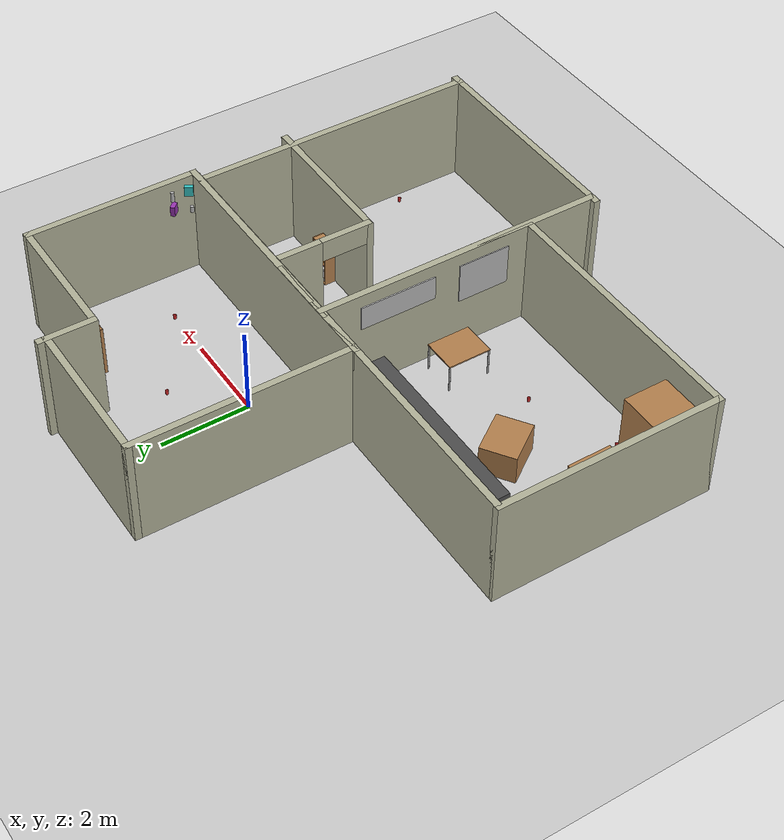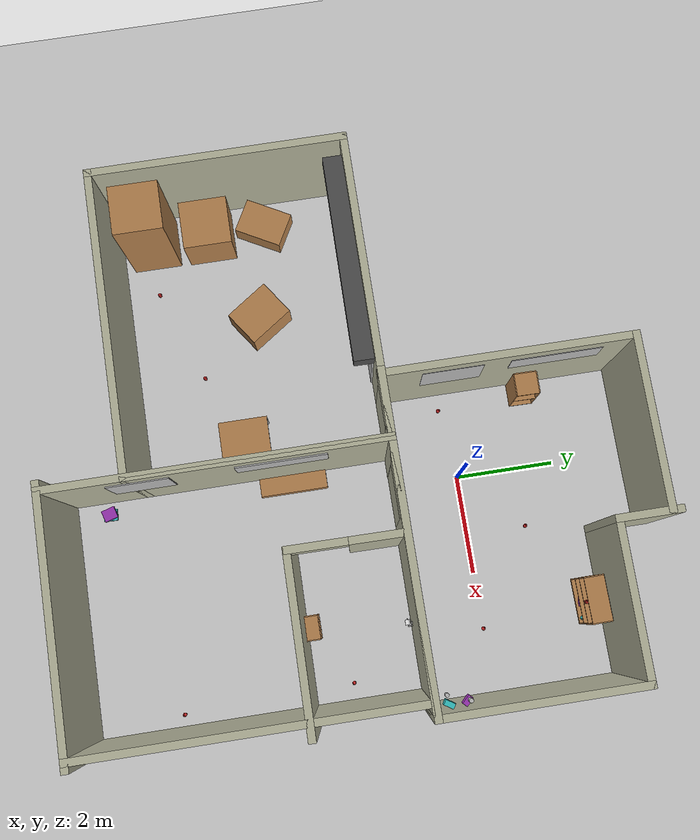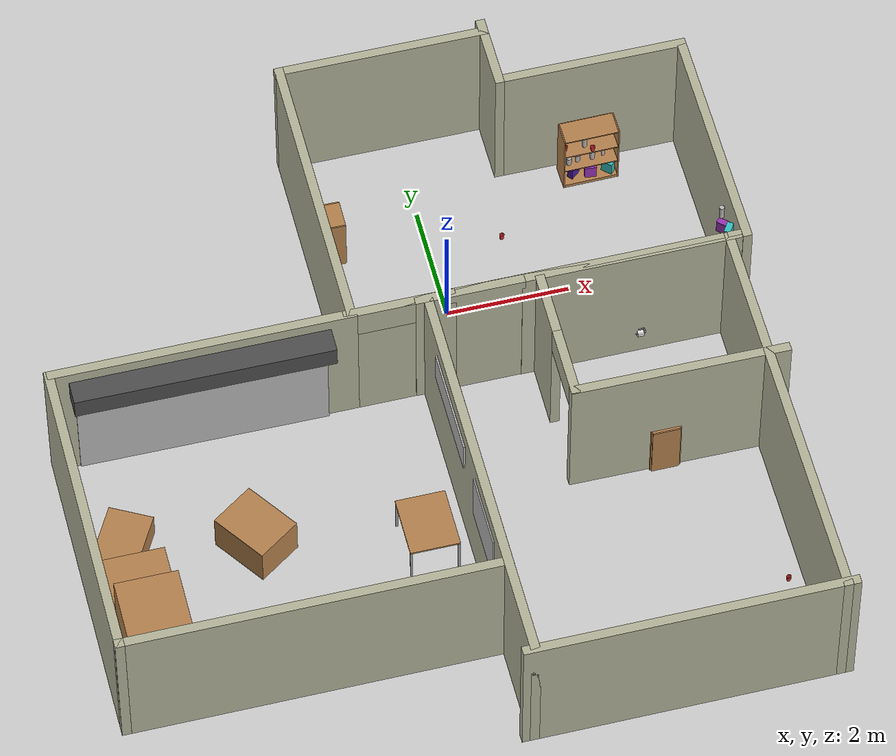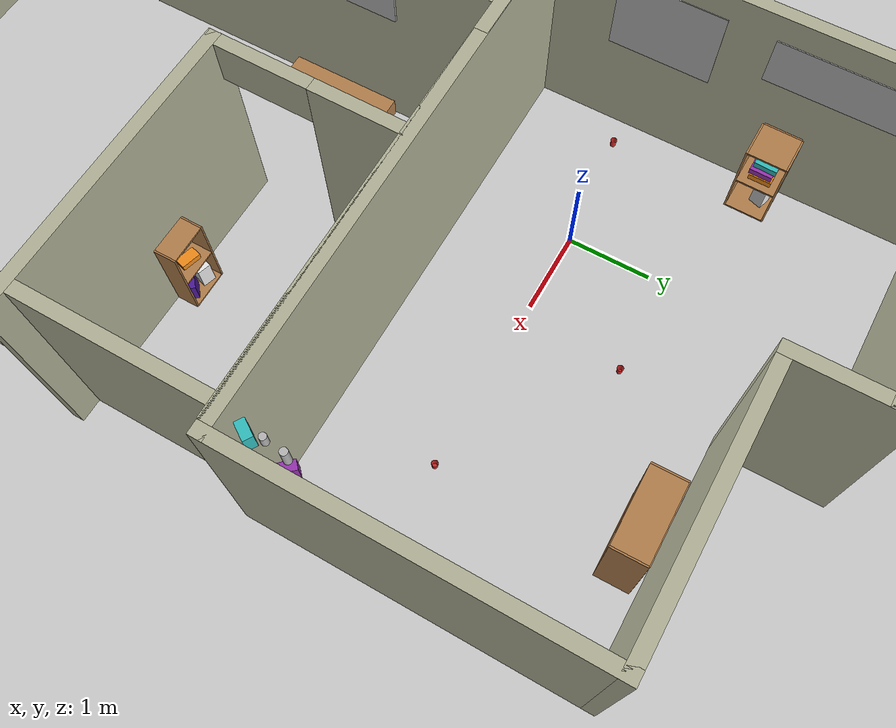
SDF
<sdf version="1.6">
 <world name="default">
  <plugin name="ros_link_attacher_plugin" filename="libgazebo_ros_link_attacher.so"/>
  <light name="sun" type="directional">
   <pose>0 0 10 0 -0 0</pose>
   <diffuse>0.8 0.8 0.8 1</diffuse>
   <specular>0.2 0.2 0.2 1</specular>
   <attenuation>
    <range>1000</range>
    <constant>0.9</constant>
    <linear>0.01</linear>
    <quadratic>0.001</quadratic>
   </attenuation>
   <direction>-0.5 0.1 -0.9</direction>
  </light>
  <model name="ground_plane">
   <static>1</static>
   <link name="link">
    <collision name="collision">
     <geometry><plane><normal>0 0 1</normal><size>20 20</size></plane></geometry>
     <surface>
      <contact><collide_bitmask>65535</collide_bitmask></contact>
      <friction><ode><mu>400</mu><mu2>50</mu2></ode></friction>
     </surface>
    </collision>
    <visual name="visual">
     <cast_shadows>0</cast_shadows>
     <geometry><plane><normal>0 0 1</normal><size>20 20</size></plane></geometry>
     <material>
      <script><uri>file://media/materials/scripts/gazebo.material</uri><name>Gazebo/Grey</name></script>
     </material>
    </visual>
   </link>
  </model>
  <gravity>0 0 -9.8</gravity>
  <magnetic_field>6e-06 2.3e-05 -4.2e-05</magnetic_field>
  <atmosphere type="adiabatic"/>
  <physics name="default_physics" default="0" type="ode">
   <max_step_size>0.001</max_step_size>
   <real_time_factor>1</real_time_factor>
   <real_time_update_rate>1000</real_time_update_rate>
  </physics>
  <scene><ambient>0.4 0.4 0.4 1</ambient><background>0.7 0.7 0.7 1</background><shadows>1</shadows></scene>
  <audio><device>default</device></audio>
  <spherical_coordinates>
   <surface_model>EARTH_WGS84</surface_model>
   <latitude_deg>0</latitude_deg>
   <longitude_deg>0</longitude_deg>
   <elevation>0</elevation>
   <heading_deg>0</heading_deg>
  </spherical_coordinates>
  <model name="kitchen_living_room_walls">
   <pose>1.30504 1.07916 0 0 -0 0</pose>
   <link name="Wall_14">
    <collision name="Wall_14_Collision">
     <geometry><box><size>5 0.15 2.5</size></box></geometry>
     <pose>0 0 1.25 0 -0 0</pose>
    </collision>
    <visual name="Wall_14_Visual">
     <pose>0 0 1.25 0 -0 0</pose>
     <geometry><box><size>5 0.15 2.5</size></box></geometry>
     <material>
      <script><uri>file://media/materials/scripts/gazebo.material</uri><name>Gazebo/Residential</name></script>
      <ambient>1 1 1 1</ambient>
     </material>
     <meta><layer>0</layer></meta>
    </visual>
    <pose>-3.175 0 0 0 -0 -1.5708</pose>
   </link>
   <link name="Wall_15">
    <collision name="Wall_15_Collision">
     <geometry><box><size>6.5 0.15 2.5</size></box></geometry>
     <pose>0 0 1.25 0 -0 0</pose>
    </collision>
    <visual name="Wall_15_Visual">
     <pose>0 0 1.25 0 -0 0</pose>
     <geometry><box><size>6.5 0.15 2.5</size></box></geometry>
     <material>
      <script><uri>file://media/materials/scripts/gazebo.material</uri><name>Gazebo/Residential</name></script>
      <ambient>1 1 1 1</ambient>
     </material>
     <meta><layer>0</layer></meta>
    </visual>
    <pose>0 -2.425 0 0 -0 0</pose>
   </link>
   <link name="Wall_16">
    <collision name="Wall_16_Collision">
     <geometry><box><size>4 0.15 2.5</size></box></geometry>
     <pose>0 0 1.25 0 -0 0</pose>
    </collision>
    <visual name="Wall_16_Visual">
     <pose>0 0 1.25 0 -0 0</pose>
     <geometry><box><size>4 0.15 2.5</size></box></geometry>
     <material>
      <script><uri>file://media/materials/scripts/gazebo.material</uri><name>Gazebo/Residential</name></script>
      <ambient>1 1 1 1</ambient>
     </material>
     <meta><layer>0</layer></meta>
    </visual>
    <pose>3.175 -0.5 0 0 -0 1.5708</pose>
   </link>
   <link name="Wall_17">
    <collision name="Wall_17_Collision">
     <geometry><box><size>3 0.15 2.5</size></box></geometry>
     <pose>0 0 1.25 0 -0 0</pose>
    </collision>
    <visual name="Wall_17_Visual">
     <pose>0 0 1.25 0 -0 0</pose>
     <geometry><box><size>3 0.15 2.5</size></box></geometry>
     <material>
      <script><uri>file://media/materials/scripts/gazebo.material</uri><name>Gazebo/Residential</name></script>
      <ambient>1 1 1 1</ambient>
     </material>
     <meta><layer>0</layer></meta>
    </visual>
    <pose>1.75 1.425 0 0 -0 3.14159</pose>
   </link>
   <link name="Wall_19">
    <collision name="Wall_19_Collision">
     <geometry><box><size>3.5 0.15 2.5</size></box></geometry>
     <pose>0 0 1.25 0 -0 0</pose>
    </collision>
    <visual name="Wall_19_Visual">
     <pose>0 0 1.25 0 -0 0</pose>
     <geometry><box><size>3.5 0.15 2.5</size></box></geometry>
     <material>
      <script><uri>file://media/materials/scripts/gazebo.material</uri><name>Gazebo/Residential</name></script>
      <ambient>1 1 1 1</ambient>
     </material>
     <meta><layer>0</layer></meta>
    </visual>
    <pose>-1.5 2.425 0 0 -0 0</pose>
   </link>
   <link name="Wall_20">
    <collision name="Wall_20_Collision">
     <geometry><box><size>1.3 0.15 2.5</size></box></geometry>
     <pose>0 0 1.25 0 -0 0</pose>
    </collision>
    <visual name="Wall_20_Visual">
     <pose>0 0 1.25 0 -0 0</pose>
     <geometry><box><size>1.3 0.15 2.5</size></box></geometry>
     <material>
      <script><uri>file://media/materials/scripts/gazebo.material</uri><name>Gazebo/Residential</name></script>
      <ambient>1 1 1 1</ambient>
     </material>
     <meta><layer>0</layer></meta>
    </visual>
    <pose>0.175 2 0 0 -0 -1.5708</pose>
   </link>
   <static>1</static>
  </model>
  <model name="bookshelf">
   <static>1</static>
   <link name="link">
    <inertial><mass>1</mass></inertial>
    <collision name="back">
     <pose>0 0.005 0.6 0 -0 0</pose>
     <geometry><box><size>0.9 0.01 1.2</size></box></geometry>
    </collision>
    <visual name="visual1">
     <pose>0 0.005 0.6 0 -0 0</pose>
     <geometry><box><size>0.9 0.01 1.2</size></box></geometry>
     <material>
      <script><uri>file://media/materials/scripts/gazebo.material</uri><name>Gazebo/Wood</name></script>
     </material>
    </visual>
    <collision name="left_side">
     <pose>0.45 -0.195 0.6 0 -0 0</pose>
     <geometry><box><size>0.02 0.4 1.2</size></box></geometry>
    </collision>
    <visual name="visual2">
     <pose>0.45 -0.195 0.6 0 -0 0</pose>
     <geometry><box><size>0.02 0.4 1.2</size></box></geometry>
     <material>
      <script><uri>file://media/materials/scripts/gazebo.material</uri><name>Gazebo/Wood</name></script>
     </material>
    </visual>
    <collision name="right_side">
     <pose>-0.45 -0.195 0.6 0 -0 0</pose>
     <geometry><box><size>0.02 0.4 1.2</size></box></geometry>
    </collision>
    <visual name="visual3">
     <pose>-0.45 -0.195 0.6 0 -0 0</pose>
     <geometry><box><size>0.02 0.4 1.2</size></box></geometry>
     <material>
      <script><uri>file://media/materials/scripts/gazebo.material</uri><name>Gazebo/Wood</name></script>
     </material>
    </visual>
    <collision name="bottom">
     <pose>0 -0.195 0.03 0 -0 0</pose>
     <geometry><box><size>0.88 0.4 0.06</size></box></geometry>
    </collision>
    <visual name="visual4">
     <pose>0 -0.195 0.03 0 -0 0</pose>
     <geometry><box><size>0.88 0.4 0.06</size></box></geometry>
     <material>
      <script><uri>file://media/materials/scripts/gazebo.material</uri><name>Gazebo/Wood</name></script>
     </material>
    </visual>
    <collision name="top">
     <pose>0 -0.195 1.19 0 -0 0</pose>
     <geometry><box><size>0.88 0.4 0.02</size></box></geometry>
    </collision>
    <visual name="visual5">
     <pose>0 -0.195 1.19 0 -0 0</pose>
     <geometry><box><size>0.88 0.4 0.02</size></box></geometry>
     <material>
      <script><uri>file://media/materials/scripts/gazebo.material</uri><name>Gazebo/Wood</name></script>
     </material>
    </visual>
    <collision name="low_shelf">
     <pose>0 -0.195 0.43 0 -0 0</pose>
     <geometry><box><size>0.88 0.4 0.02</size></box></geometry>
    </collision>
    <visual name="visual6">
     <pose>0 -0.195 0.43 0 -0 0</pose>
     <geometry><box><size>0.88 0.4 0.02</size></box></geometry>
     <material>
      <script><uri>file://media/materials/scripts/gazebo.material</uri><name>Gazebo/Wood</name></script>
     </material>
    </visual>
    <collision name="high_shelf">
     <pose>0 -0.195 0.8 0 -0 0</pose>
     <geometry><box><size>0.88 0.4 0.02</size></box></geometry>
    </collision>
    <visual name="visual7">
     <pose>0 -0.195 0.8 0 -0 0</pose>
     <geometry><box><size>0.88 0.4 0.02</size></box></geometry>
     <material>
      <script><uri>file://media/materials/scripts/gazebo.material</uri><name>Gazebo/Wood</name></script>
     </material>
    </visual>
    <velocity_decay><linear>0</linear><angular>0</angular></velocity_decay>
   </link>
   <pose>2.88901 2.34907 0 0 -0 0.011886</pose>
  </model>
  <model name="cabinet">
   <static>1</static>
   <link name="cabinet_bottom_plate">
    <inertial>
     <pose>0 0 -1 0 -0 0</pose>
     <inertia><ixx>2.05</ixx><ixy>0</ixy><ixz>0</ixz><iyy>2.05</iyy><iyz>0</iyz><izz>2.05</izz></inertia>
     <mass>25</mass>
    </inertial>
    <collision name="cabinet_bottom_plate_geom">
     <pose>0 0 0.01 0 -0 0</pose>
     <geometry><box><size>0.45 0.45 0.02</size></box></geometry>
    </collision>
    <visual name="cabinet_bottom_plate_geom_visual">
     <pose>0 0 0.01 0 -0 0</pose>
     <geometry><box><size>0.45 0.45 0.02</size></box></geometry>
     <material>
      <script><uri>file://media/materials/scripts/gazebo.material</uri><name>Gazebo/Wood</name></script>
     </material>
    </visual>
    <collision name="cabinet_bottom_plate_geom_cabinet_back_plate">
     <pose>0.235 0 0.51 0 -0 0</pose>
     <geometry><box><size>0.02 0.45 1.02</size></box></geometry>
    </collision>
    <visual name="cabinet_bottom_plate_geom_cabinet_back_plate_visual">
     <pose>0.235 0 0.51 0 -0 0</pose>
     <geometry><box><size>0.02 0.45 1.02</size></box></geometry>
     <material>
      <script><uri>file://media/materials/scripts/gazebo.material</uri><name>Gazebo/Wood</name></script>
     </material>
    </visual>
    <collision name="cabinet_bottom_plate_geom_cabinet_left_plate">
     <pose>0 0.235 0.51 0 -0 0</pose>
     <geometry><box><size>0.45 0.02 1.02</size></box></geometry>
    </collision>
    <visual name="cabinet_bottom_plate_geom_cabinet_left_plate_visual">
     <pose>0 0.235 0.51 0 -0 0</pose>
     <geometry><box><size>0.45 0.02 1.02</size></box></geometry>
     <material>
      <script><uri>file://media/materials/scripts/gazebo.material</uri><name>Gazebo/Wood</name></script>
     </material>
    </visual>
    <collision name="cabinet_bottom_plate_geom_cabinet_middle_plate">
     <pose>0 0 0.51 0 -0 0</pose>
     <geometry><box><size>0.45 0.45 0.02</size></box></geometry>
    </collision>
    <visual name="cabinet_bottom_plate_geom_cabinet_middle_plate_visual">
     <pose>0 0 0.51 0 -0 0</pose>
     <geometry><box><size>0.45 0.45 0.02</size></box></geometry>
     <material>
      <script><uri>file://media/materials/scripts/gazebo.material</uri><name>Gazebo/Wood</name></script>
     </material>
    </visual>
    <collision name="cabinet_bottom_plate_geom_cabinet_right_plate">
     <pose>0 -0.235 0.51 0 -0 0</pose>
     <geometry><box><size>0.45 0.02 1.02</size></box></geometry>
    </collision>
    <visual name="cabinet_bottom_plate_geom_cabinet_right_plate_visual">
     <pose>0 -0.235 0.51 0 -0 0</pose>
     <geometry><box><size>0.45 0.02 1.02</size></box></geometry>
     <material>
      <script><uri>file://media/materials/scripts/gazebo.material</uri><name>Gazebo/Wood</name></script>
     </material>
    </visual>
    <collision name="cabinet_bottom_plate_geom_cabinet_top_plate">
     <pose>0 0 1.01 0 -0 0</pose>
     <geometry><box><size>0.45 0.45 0.02</size></box></geometry>
    </collision>
    <visual name="cabinet_bottom_plate_geom_cabinet_top_plate_visual">
     <pose>0 0 1.01 0 -0 0</pose>
     <geometry><box><size>0.45 0.45 0.02</size></box></geometry>
     <material>
      <script><uri>file://media/materials/scripts/gazebo.material</uri><name>Gazebo/Wood</name></script>
     </material>
    </visual>
    <velocity_decay><linear>0</linear><angular>0</angular></velocity_decay>
   </link>
   <pose>-1.54168 1.59926 0 0 -0 3.12905</pose>
  </model>
  <model name="unit_box_0">
   <pose>2.91022 2.06442 0.177873 0 -0 1.4611</pose>
   <link name="link">
    <inertial>
     <mass>1</mass>
     <inertia>
      <ixx>0.166667</ixx>
      <ixy>0</ixy>
      <ixz>0</ixz>
      <iyy>0.166667</iyy>
      <iyz>0</iyz>
      <izz>0.166667</izz>
     </inertia>
    </inertial>
    <collision name="collision"><geometry><box><size>0.103337 0.19266 0.235754</size></box></geometry></collision>
    <visual name="visual">
     <geometry><box><size>0.103337 0.19266 0.235754</size></box></geometry>
     <material>
      <script><name>Gazebo/Purple</name><uri>file://media/materials/scripts/gazebo.material</uri></script>
     </material>
    </visual>
   </link>
  </model>
  <model name="unit_box_0_clone">
   <pose>3.20796 2.08529 0.177871 0 -0 0.810944</pose>
   <link name="link">
    <inertial>
     <mass>1</mass>
     <inertia>
      <ixx>0.166667</ixx>
      <ixy>0</ixy>
      <ixz>0</ixz>
      <iyy>0.166667</iyy>
      <iyz>0</iyz>
      <izz>0.166667</izz>
     </inertia>
    </inertial>
    <collision name="collision"><geometry><box><size>0.103337 0.19266 0.235754</size></box></geometry></collision>
    <visual name="visual">
     <geometry><box><size>0.103337 0.19266 0.235754</size></box></geometry>
     <material>
      <script><name>Gazebo/Turquoise</name><uri>file://media/materials/scripts/gazebo.material</uri></script>
     </material>
    </visual>
   </link>
  </model>
  <model name="unit_box_0_clone_0">
   <pose>2.64663 2.13879 0.177874 -1e-06 1e-06 -0.868392</pose>
   <link name="link">
    <inertial>
     <mass>1</mass>
     <inertia>
      <ixx>0.166667</ixx>
      <ixy>0</ixy>
      <ixz>0</ixz>
      <iyy>0.166667</iyy>
      <iyz>0</iyz>
      <izz>0.166667</izz>
     </inertia>
    </inertial>
    <collision name="collision"><geometry><box><size>0.103337 0.19266 0.235754</size></box></geometry></collision>
    <visual name="visual">
     <geometry><box><size>0.103337 0.19266 0.235754</size></box></geometry>
     <material>
      <script><name>Gazebo/Indigo</name><uri>file://media/materials/scripts/gazebo.material</uri></script>
     </material>
    </visual>
   </link>
  </model>
  <model name="sprite">
   <static>0</static>
   <link name="link">
    <inertial>
     <mass>0.25</mass>
     <inertia><ixx>0</ixx><ixy>0</ixy><ixz>0</ixz><iyy>0</iyy><iyz>0</iyz><izz>0</izz></inertia>
    </inertial>
    <collision name="collision">
     <pose>0 0 0.075 -3.14159 -0 0</pose>
     <geometry><cylinder><radius>0.04</radius><length>0.15</length></cylinder></geometry>
    </collision>
    <visual name="visual">
     <pose>0 0 0.075 -3.14159 -0 0</pose>
     <geometry><cylinder><radius>0.04</radius><length>0.15</length></cylinder></geometry>
     <material>
      <script>
       <uri>model://sprite/material/scripts</uri>
       <uri>model://sprite/material/textures</uri>
       <name>Custom/sprite</name>
      </script>
     </material>
    </visual>
    <velocity_decay><linear>0</linear><angular>0</angular></velocity_decay>
   </link>
   <pose>2.55298 2.08461 0.440008 -0.000126 -0.000168 -5.5e-05</pose>
  </model>
  <model name="cocacola">
   <static>0</static>
   <link name="link">
    <inertial>
     <mass>0.25</mass>
     <inertia><ixx>0</ixx><ixy>0</ixy><ixz>0</ixz><iyy>0</iyy><iyz>0</iyz><izz>0</izz></inertia>
    </inertial>
    <collision name="collision">
     <pose>0 0 0.075 -3.14159 -0 0</pose>
     <geometry><cylinder><radius>0.04</radius><length>0.15</length></cylinder></geometry>
    </collision>
    <visual name="visual">
     <pose>0 0 0.075 -3.14159 -0 0</pose>
     <geometry><cylinder><radius>0.04</radius><length>0.15</length></cylinder></geometry>
     <material>
      <script>
       <uri>model://cocacola/material/scripts</uri>
       <uri>model://cocacola/material/textures</uri>
       <name>Custom/cocacola</name>
      </script>
     </material>
    </visual>
    <velocity_decay><linear>0</linear><angular>0</angular></velocity_decay>
   </link>
   <pose>2.70315 2.11913 0.44001 -0.000179 0.000163 -7e-05</pose>
  </model>
  <model name="coke_can_slim">
   <static>0</static>
   <link name="link">
    <inertial>
     <mass>0.15</mass>
     <inertia><ixx>2079.98</ixx><ixy>0</ixy><ixz>0</ixz><iyy>2079.98</iyy><iyz>0</iyz><izz>419.21</izz></inertia>
    </inertial>
    <collision name="collision">
     <geometry><cylinder><radius>0.029</radius><length>0.15</length></cylinder></geometry>
    </collision>
    <visual name="visual">
     <geometry><cylinder><radius>0.029</radius><length>0.15</length></cylinder></geometry>
     <material>
      <script>
       <uri>model://coke_can_slim/material/scripts</uri>
       <uri>model://coke_can_slim/material/textures</uri>
       <name>Custom/coke_can_slim</name>
      </script>
     </material>
    </visual>
    <velocity_decay><linear>0</linear><angular>0</angular></velocity_decay>
   </link>
   <pose>3.13415 2.14019 0.514999 -0.000298 3.5e-05 0</pose>
  </model>
  <model name="pringles2">
   <static>0</static>
   <link name="link">
    <inertial>
     <mass>0.25</mass>
     <inertia><ixx>0</ixx><ixy>0</ixy><ixz>0</ixz><iyy>0</iyy><iyz>0</iyz><izz>0</izz></inertia>
    </inertial>
    <collision name="collision">
     <pose>0 0 0.12 -3.14159 -0 0</pose>
     <geometry><cylinder><radius>0.04</radius><length>0.235</length></cylinder></geometry>
    </collision>
    <visual name="visual">
     <pose>0 0 0.12 -3.14159 -0 0</pose>
     <geometry><cylinder><radius>0.04</radius><length>0.235</length></cylinder></geometry>
     <material>
      <script>
       <uri>model://pringles2/material/scripts</uri>
       <uri>model://pringles2/material/textures</uri>
       <name>Custom/pringles2</name>
      </script>
     </material>
    </visual>
    <velocity_decay><linear>0</linear><angular>0</angular></velocity_decay>
   </link>
   <pose>2.949 2.11273 0.437493 8e-06 6.4e-05 0.001154</pose>
  </model>
  <model name="pringles">
   <static>0</static>
   <link name="link">
    <inertial>
     <mass>0.25</mass>
     <inertia><ixx>0</ixx><ixy>0</ixy><ixz>0</ixz><iyy>0</iyy><iyz>0</iyz><izz>0</izz></inertia>
    </inertial>
    <collision name="collision">
     <geometry><cylinder><radius>0.04</radius><length>0.235</length></cylinder></geometry>
    </collision>
    <visual name="visual">
     <geometry><cylinder><radius>0.04</radius><length>0.235</length></cylinder></geometry>
     <material>
      <script>
       <uri>model://pringles/material/scripts</uri>
       <uri>model://pringles/material/textures</uri>
       <name>Custom/pringles</name>
      </script>
     </material>
    </visual>
    <velocity_decay><linear>0</linear><angular>0</angular></velocity_decay>
   </link>
   <pose>2.81279 2.11198 0.927495 -6e-05 9.4e-05 -0.001067</pose>
  </model>
  <model name="cup_glass_test">
   <link name="link_0">
    <inertial>
     <mass>0.0510344</mass>
     <inertia>
      <ixx>5.22719e-05</ixx>
      <ixy>0</ixy>
      <ixz>0</ixz>
      <iyy>5.22719e-05</iyy>
      <iyz>0</iyz>
      <izz>3.65038e-05</izz>
     </inertia>
     <pose>0 0 0.048 0 -0 0</pose>
    </inertial>
    <visual name="visual">
     <geometry><mesh><uri>model://cup_glass_test/meshes/cup_glass.dae</uri><scale>1 1 1</scale></mesh></geometry>
     <material>
      <lighting>1</lighting>
      <script><uri>file://media/materials/scripts/gazebo.material</uri><name>Gazebo/Red</name></script>
     </material>
    </visual>
    <collision name="collision">
     <geometry><mesh><uri>model://cup_glass_test/meshes/cup_glass.dae</uri><scale>1 1 1</scale></mesh></geometry>
     <surface>
      <friction>
       <ode><mu>1</mu><mu2>1</mu2><fdir1>0 0 0</fdir1><slip1>0</slip1><slip2>0</slip2></ode>
       <torsional>
        <coefficient>1</coefficient>
        <patch_radius>0</patch_radius>
        <surface_radius>0</surface_radius>
        <use_patch_radius>1</use_patch_radius>
        <ode><slip>0</slip></ode>
       </torsional>
      </friction>
      <bounce><restitution_coefficient>0</restitution_coefficient><threshold>1e+06</threshold></bounce>
      <contact>
       <collide_without_contact>0</collide_without_contact>
       <collide_without_contact_bitmask>1</collide_without_contact_bitmask>
       <collide_bitmask>1</collide_bitmask>
       <ode>
        <soft_cfm>0</soft_cfm>
        <soft_erp>0.2</soft_erp>
        <kp>1e+13</kp>
        <kd>1</kd>
        <max_vel>0.01</max_vel>
        <min_depth>0</min_depth>
       </ode>
       <bullet>
        <split_impulse>1</split_impulse>
        <split_impulse_penetration_threshold>-0.01</split_impulse_penetration_threshold>
        <soft_cfm>0</soft_cfm>
        <soft_erp>0.2</soft_erp>
        <kp>1e+13</kp>
        <kd>1</kd>
       </bullet>
      </contact>
     </surface>
    </collision>
   </link>
   <static>0</static>
   <pose>2.91796 1.99162 0.809318 -0.014445 -0.014271 0.093986</pose>
  </model>
  <model name="cup_glass_test_0">
   <link name="link_0">
    <inertial>
     <mass>0.0510344</mass>
     <inertia>
      <ixx>5.22719e-05</ixx>
      <ixy>0</ixy>
      <ixz>0</ixz>
      <iyy>5.22719e-05</iyy>
      <iyz>0</iyz>
      <izz>3.65038e-05</izz>
     </inertia>
     <pose>0 0 0.048 0 -0 0</pose>
    </inertial>
    <visual name="visual">
     <geometry><mesh><uri>model://cup_glass_test/meshes/cup_glass.dae</uri><scale>1 1 1</scale></mesh></geometry>
     <material>
      <lighting>1</lighting>
      <script><uri>file://media/materials/scripts/gazebo.material</uri><name>Gazebo/Red</name></script>
     </material>
    </visual>
    <collision name="collision">
     <geometry><mesh><uri>model://cup_glass_test/meshes/cup_glass.dae</uri><scale>1 1 1</scale></mesh></geometry>
     <surface>
      <friction>
       <ode><mu>1</mu><mu2>1</mu2><fdir1>0 0 0</fdir1><slip1>0</slip1><slip2>0</slip2></ode>
       <torsional>
        <coefficient>1</coefficient>
        <patch_radius>0</patch_radius>
        <surface_radius>0</surface_radius>
        <use_patch_radius>1</use_patch_radius>
        <ode><slip>0</slip></ode>
       </torsional>
      </friction>
      <bounce><restitution_coefficient>0</restitution_coefficient><threshold>1e+06</threshold></bounce>
      <contact>
       <collide_without_contact>0</collide_without_contact>
       <collide_without_contact_bitmask>1</collide_without_contact_bitmask>
       <collide_bitmask>1</collide_bitmask>
       <ode>
        <soft_cfm>0</soft_cfm>
        <soft_erp>0.2</soft_erp>
        <kp>1e+13</kp>
        <kd>1</kd>
        <max_vel>0.01</max_vel>
        <min_depth>0</min_depth>
       </ode>
       <bullet>
        <split_impulse>1</split_impulse>
        <split_impulse_penetration_threshold>-0.01</split_impulse_penetration_threshold>
        <soft_cfm>0</soft_cfm>
        <soft_erp>0.2</soft_erp>
        <kp>1e+13</kp>
        <kd>1</kd>
       </bullet>
      </contact>
     </surface>
    </collision>
   </link>
   <static>0</static>
   <pose>2.48303 2.097 0.81171 -0.008596 0.065626 0.085069</pose>
  </model>
  <model name="cup_glass_test_1">
   <link name="link_0">
    <inertial>
     <mass>0.0510344</mass>
     <inertia>
      <ixx>5.22719e-05</ixx>
      <ixy>0</ixy>
      <ixz>0</ixz>
      <iyy>5.22719e-05</iyy>
      <iyz>0</iyz>
      <izz>3.65038e-05</izz>
     </inertia>
     <pose>0 0 0.048 0 -0 0</pose>
    </inertial>
    <visual name="visual">
     <geometry><mesh><uri>model://cup_glass_test/meshes/cup_glass.dae</uri><scale>1 1 1</scale></mesh></geometry>
     <material>
      <lighting>1</lighting>
      <script><uri>file://media/materials/scripts/gazebo.material</uri><name>Gazebo/Red</name></script>
     </material>
    </visual>
    <collision name="collision">
     <geometry><mesh><uri>model://cup_glass_test/meshes/cup_glass.dae</uri><scale>1 1 1</scale></mesh></geometry>
     <surface>
      <friction>
       <ode><mu>1</mu><mu2>1</mu2><fdir1>0 0 0</fdir1><slip1>0</slip1><slip2>0</slip2></ode>
       <torsional>
        <coefficient>1</coefficient>
        <patch_radius>0</patch_radius>
        <surface_radius>0</surface_radius>
        <use_patch_radius>1</use_patch_radius>
        <ode><slip>0</slip></ode>
       </torsional>
      </friction>
      <bounce><restitution_coefficient>0</restitution_coefficient><threshold>1e+06</threshold></bounce>
      <contact>
       <collide_without_contact>0</collide_without_contact>
       <collide_without_contact_bitmask>1</collide_without_contact_bitmask>
       <collide_bitmask>1</collide_bitmask>
       <ode>
        <soft_cfm>0</soft_cfm>
        <soft_erp>0.2</soft_erp>
        <kp>1e+13</kp>
        <kd>1</kd>
        <max_vel>0.01</max_vel>
        <min_depth>0</min_depth>
       </ode>
       <bullet>
        <split_impulse>1</split_impulse>
        <split_impulse_penetration_threshold>-0.01</split_impulse_penetration_threshold>
        <soft_cfm>0</soft_cfm>
        <soft_erp>0.2</soft_erp>
        <kp>1e+13</kp>
        <kd>1</kd>
       </bullet>
      </contact>
     </surface>
    </collision>
   </link>
   <static>0</static>
   <pose>3.14225 0.005421 -0.000682 -0.014436 -0.014242 1.10712</pose>
  </model>
  <model name="cup_glass_test_2">
   <link name="link_0">
    <inertial>
     <mass>0.0510344</mass>
     <inertia>
      <ixx>5.22719e-05</ixx>
      <ixy>0</ixy>
      <ixz>0</ixz>
      <iyy>5.22719e-05</iyy>
      <iyz>0</iyz>
      <izz>3.65038e-05</izz>
     </inertia>
     <pose>0 0 0.048 0 -0 0</pose>
    </inertial>
    <visual name="visual">
     <geometry><mesh><uri>model://cup_glass_test/meshes/cup_glass.dae</uri><scale>1 1 1</scale></mesh></geometry>
     <material>
      <lighting>1</lighting>
      <script><uri>file://media/materials/scripts/gazebo.material</uri><name>Gazebo/Red</name></script>
     </material>
    </visual>
    <collision name="collision">
     <geometry><mesh><uri>model://cup_glass_test/meshes/cup_glass.dae</uri><scale>1 1 1</scale></mesh></geometry>
     <surface>
      <friction>
       <ode><mu>1</mu><mu2>1</mu2><fdir1>0 0 0</fdir1><slip1>0</slip1><slip2>0</slip2></ode>
       <torsional>
        <coefficient>1</coefficient>
        <patch_radius>0</patch_radius>
        <surface_radius>0</surface_radius>
        <use_patch_radius>1</use_patch_radius>
        <ode><slip>0</slip></ode>
       </torsional>
      </friction>
      <bounce><restitution_coefficient>0</restitution_coefficient><threshold>1e+06</threshold></bounce>
      <contact>
       <collide_without_contact>0</collide_without_contact>
       <collide_without_contact_bitmask>1</collide_without_contact_bitmask>
       <collide_bitmask>1</collide_bitmask>
       <ode>
        <soft_cfm>0</soft_cfm>
        <soft_erp>0.2</soft_erp>
        <kp>1e+13</kp>
        <kd>1</kd>
        <max_vel>0.01</max_vel>
        <min_depth>0</min_depth>
       </ode>
       <bullet>
        <split_impulse>1</split_impulse>
        <split_impulse_penetration_threshold>-0.01</split_impulse_penetration_threshold>
        <soft_cfm>0</soft_cfm>
        <soft_erp>0.2</soft_erp>
        <kp>1e+13</kp>
        <kd>1</kd>
       </bullet>
      </contact>
     </surface>
    </collision>
   </link>
   <static>0</static>
   <pose>1.21724 1.22054 -0.000684 -0.01444 -0.014343 1.15451</pose>
  </model>
  <model name="cup_glass_test_3">
   <link name="link_0">
    <inertial>
     <mass>0.0510344</mass>
     <inertia>
      <ixx>5.22719e-05</ixx>
      <ixy>0</ixy>
      <ixz>0</ixz>
      <iyy>5.22719e-05</iyy>
      <iyz>0</iyz>
      <izz>3.65038e-05</izz>
     </inertia>
     <pose>0 0 0.048 0 -0 0</pose>
    </inertial>
    <visual name="visual">
     <geometry><mesh><uri>model://cup_glass_test/meshes/cup_glass.dae</uri><scale>1 1 1</scale></mesh></geometry>
     <material>
      <lighting>1</lighting>
      <script><uri>file://media/materials/scripts/gazebo.material</uri><name>Gazebo/Red</name></script>
     </material>
    </visual>
    <collision name="collision">
     <geometry><mesh><uri>model://cup_glass_test/meshes/cup_glass.dae</uri><scale>1 1 1</scale></mesh></geometry>
     <surface>
      <friction>
       <ode><mu>1</mu><mu2>1</mu2><fdir1>0 0 0</fdir1><slip1>0</slip1><slip2>0</slip2></ode>
       <torsional>
        <coefficient>1</coefficient>
        <patch_radius>0</patch_radius>
        <surface_radius>0</surface_radius>
        <use_patch_radius>1</use_patch_radius>
        <ode><slip>0</slip></ode>
       </torsional>
      </friction>
      <bounce><restitution_coefficient>0</restitution_coefficient><threshold>1e+06</threshold></bounce>
      <contact>
       <collide_without_contact>0</collide_without_contact>
       <collide_without_contact_bitmask>1</collide_without_contact_bitmask>
       <collide_bitmask>1</collide_bitmask>
       <ode>
        <soft_cfm>0</soft_cfm>
        <soft_erp>0.2</soft_erp>
        <kp>1e+13</kp>
        <kd>1</kd>
        <max_vel>0.01</max_vel>
        <min_depth>0</min_depth>
       </ode>
       <bullet>
        <split_impulse>1</split_impulse>
        <split_impulse_penetration_threshold>-0.01</split_impulse_penetration_threshold>
        <soft_cfm>0</soft_cfm>
        <soft_erp>0.2</soft_erp>
        <kp>1e+13</kp>
        <kd>1</kd>
       </bullet>
      </contact>
     </surface>
    </collision>
   </link>
   <static>0</static>
   <pose>-1.43676 -0.152813 -0.000684 -0.014465 -0.014205 1.24896</pose>
  </model>
  <model name="unit_box_1">
   <pose>-1.56462 1.68692 0.166864 -2e-06 -2e-06 -0.308094</pose>
   <link name="link">
    <inertial>
     <mass>1</mass>
     <inertia>
      <ixx>0.166667</ixx>
      <ixy>0</ixy>
      <ixz>0</ixz>
      <iyy>0.166667</iyy>
      <iyz>0</iyz>
      <izz>0.166667</izz>
     </inertia>
    </inertial>
    <collision name="collision"><geometry><box><size>0.157314 0.16474 0.293728</size></box></geometry></collision>
    <visual name="visual">
     <geometry><box><size>0.157314 0.16474 0.293728</size></box></geometry>
     <material>
      <script><name>Gazebo/White</name><uri>file://media/materials/scripts/gazebo.material</uri></script>
     </material>
    </visual>
   </link>
  </model>
  <model name="unit_box">
   <pose>-1.52024 1.60563 0.554916 0 0 -0.006062</pose>
   <link name="link">
    <inertial>
     <mass>1</mass>
     <inertia>
      <ixx>0.166667</ixx>
      <ixy>0</ixy>
      <ixz>0</ixz>
      <iyy>0.166667</iyy>
      <iyz>0</iyz>
      <izz>0.166667</izz>
     </inertia>
    </inertial>
    <collision name="collision"><geometry><box><size>0.230096 0.26666 0.069832</size></box></geometry></collision>
    <visual name="visual">
     <geometry><box><size>0.230096 0.26666 0.069832</size></box></geometry>
     <material>
      <script><name>Gazebo/Orange</name><uri>file://media/materials/scripts/gazebo.material</uri></script>
     </material>
    </visual>
   </link>
  </model>
  <model name="unit_box_clone_0">
   <pose>-1.58461 1.60891 0.694567 -4.7e-05 -3.7e-05 -0.035696</pose>
   <link name="link">
    <inertial>
     <mass>1</mass>
     <inertia>
      <ixx>0.166667</ixx>
      <ixy>0</ixy>
      <ixz>0</ixz>
      <iyy>0.166667</iyy>
      <iyz>0</iyz>
      <izz>0.166667</izz>
     </inertia>
    </inertial>
    <collision name="collision">
     <geometry><box><size>0.230096 0.266659 0.069832</size></box></geometry>
    </collision>
    <visual name="visual">
     <geometry><box><size>0.230096 0.266659 0.069832</size></box></geometry>
     <material>
      <script><name>Gazebo/Turquoise</name><uri>file://media/materials/scripts/gazebo.material</uri></script>
     </material>
    </visual>
   </link>
  </model>
  <model name="unit_box_clone_1">
   <pose>-1.53781 1.59018 0.624738 -4.3e-05 -4.3e-05 -0.021511</pose>
   <link name="link">
    <inertial>
     <mass>1</mass>
     <inertia>
      <ixx>0.166667</ixx>
      <ixy>0</ixy>
      <ixz>0</ixz>
      <iyy>0.166667</iyy>
      <iyz>0</iyz>
      <izz>0.166667</izz>
     </inertia>
    </inertial>
    <collision name="collision">
     <geometry><box><size>0.230096 0.266659 0.069832</size></box></geometry>
    </collision>
    <visual name="visual">
     <geometry><box><size>0.230096 0.266659 0.069832</size></box></geometry>
     <material>
      <script><name>Gazebo/Purple</name><uri>file://media/materials/scripts/gazebo.material</uri></script>
     </material>
    </visual>
   </link>
  </model>
  <model name="ufrgs_poster">
   <link name="link">
    <visual name="visual">
     <geometry><box><size>0.03 1.20154 0.949467</size></box></geometry>
     <material>
      <script>
       <uri>model://ufrgs_poster/material/script</uri>
       <uri>model://ufrgs_poster/material/textures</uri>
       <name>Custom/ufrgs_logo</name>
      </script>
     </material>
    </visual>
   </link>
   <static>1</static>
   <pose>-1.8013 0.035665 1.71741 0 -0 0</pose>
  </model>
  <model name="uio_poster">
   <link name="link">
    <visual name="visual">
     <geometry><box><size>0.03 1.76931 0.56609</size></box></geometry>
     <material>
      <script>
       <uri>model://uio_poster/material/script</uri>
       <uri>model://uio_poster/material/textures</uri>
       <name>Custom/uio_logo</name>
      </script>
     </material>
    </visual>
   </link>
   <static>1</static>
   <pose>-1.79613 2.0446 1.91099 0 -0 0</pose>
  </model>
  <model name="unit_box_0_clone_1">
   <pose>4.29697 -0.725867 1.88099 1e-06 1e-06 0.766581</pose>
   <link name="link">
    <inertial>
     <mass>1</mass>
     <inertia>
      <ixx>0.166667</ixx>
      <ixy>0</ixy>
      <ixz>0</ixz>
      <iyy>0.166667</iyy>
      <iyz>0</iyz>
      <izz>0.166667</izz>
     </inertia>
    </inertial>
    <collision name="collision"><geometry><box><size>0.103337 0.19266 0.235754</size></box></geometry></collision>
    <visual name="visual">
     <geometry><box><size>0.103337 0.19266 0.235754</size></box></geometry>
     <material>
      <script><name>Gazebo/Purple</name><uri>file://media/materials/scripts/gazebo.material</uri></script>
     </material>
    </visual>
   </link>
  </model>
  <model name="unit_box_0_clone_clone">
   <pose>4.26957 -1.09406 2.24483 -0 9e-06 -0.576163</pose>
   <link name="link">
    <inertial>
     <mass>1</mass>
     <inertia>
      <ixx>0.166667</ixx>
      <ixy>0</ixy>
      <ixz>0</ixz>
      <iyy>0.166667</iyy>
      <iyz>0</iyz>
      <izz>0.166667</izz>
     </inertia>
    </inertial>
    <collision name="collision"><geometry><box><size>0.103337 0.19266 0.235754</size></box></geometry></collision>
    <visual name="visual">
     <geometry><box><size>0.103337 0.19266 0.235754</size></box></geometry>
     <material>
      <script><name>Gazebo/Turquoise</name><uri>file://media/materials/scripts/gazebo.material</uri></script>
     </material>
    </visual>
   </link>
  </model>
  <model name="cocacola_clone">
   <static>0</static>
   <link name="link">
    <inertial>
     <mass>0.25</mass>
     <inertia><ixx>0</ixx><ixy>0</ixy><ixz>0</ixz><iyy>0</iyy><iyz>0</iyz><izz>0</izz></inertia>
    </inertial>
    <collision name="collision">
     <pose>0 0 0.075 -3.14159 -0 0</pose>
     <geometry><cylinder><radius>0.04</radius><length>0.15</length></cylinder></geometry>
    </collision>
    <visual name="visual">
     <pose>0 0 0.075 -3.14159 -0 0</pose>
     <geometry><cylinder><radius>0.04</radius><length>0.15</length></cylinder></geometry>
     <material>
      <script>
       <uri>model://cocacola/material/scripts</uri>
       <uri>model://cocacola/material/textures</uri>
       <name>Custom/cocacola</name>
      </script>
     </material>
    </visual>
    <velocity_decay><linear>0</linear><angular>0</angular></velocity_decay>
   </link>
   <pose>4.15023 -1.08171 1.76313 0.000147 -3.7e-05 5.2e-05</pose>
  </model>
  <model name="pringles_clone">
   <static>0</static>
   <link name="link">
    <inertial>
     <mass>0.25</mass>
     <inertia><ixx>0</ixx><ixy>0</ixy><ixz>0</ixz><iyy>0</iyy><iyz>0</iyz><izz>0</izz></inertia>
    </inertial>
    <collision name="collision">
     <geometry><cylinder><radius>0.04</radius><length>0.235</length></cylinder></geometry>
    </collision>
    <visual name="visual">
     <geometry><cylinder><radius>0.04</radius><length>0.235</length></cylinder></geometry>
     <material>
      <script>
       <uri>model://pringles/material/scripts</uri>
       <uri>model://pringles/material/textures</uri>
       <name>Custom/pringles</name>
      </script>
     </material>
    </visual>
    <velocity_decay><linear>0</linear><angular>0</angular></velocity_decay>
   </link>
   <pose>4.26684 -0.701088 2.24446 -7e-05 0.000201 -0.002037</pose>
  </model>
  <model name="table">
   <static>1</static>
   <link name="link">
    <collision name="surface">
     <pose>0 0 0.8 0 -0 0</pose>
     <geometry><box><size>1 0.8 0.03</size></box></geometry>
    </collision>
    <visual name="visual1">
     <pose>0 0 0.8 0 -0 0</pose>
     <geometry><box><size>1 0.8 0.03</size></box></geometry>
     <material>
      <script><uri>file://media/materials/scripts/gazebo.material</uri><name>Gazebo/Wood</name></script>
     </material>
    </visual>
    <collision name="front_left_leg">
     <pose>0.48 0.38 0.4 0 -0 0</pose>
     <geometry><cylinder><radius>0.02</radius><length>0.8</length></cylinder></geometry>
    </collision>
    <visual name="front_left_leg">
     <pose>0.48 0.38 0.4 0 -0 0</pose>
     <geometry><cylinder><radius>0.02</radius><length>0.8</length></cylinder></geometry>
     <material>
      <script><uri>file://media/materials/scripts/gazebo.material</uri><name>Gazebo/Grey</name></script>
     </material>
    </visual>
    <collision name="front_right_leg">
     <pose>0.48 -0.38 0.4 0 -0 0</pose>
     <geometry><cylinder><radius>0.02</radius><length>0.8</length></cylinder></geometry>
    </collision>
    <visual name="front_right_leg">
     <pose>0.48 -0.38 0.4 0 -0 0</pose>
     <geometry><cylinder><radius>0.02</radius><length>0.8</length></cylinder></geometry>
     <material>
      <script><uri>file://media/materials/scripts/gazebo.material</uri><name>Gazebo/Grey</name></script>
     </material>
    </visual>
    <collision name="back_right_leg">
     <pose>-0.48 -0.38 0.4 0 -0 0</pose>
     <geometry><cylinder><radius>0.02</radius><length>0.8</length></cylinder></geometry>
    </collision>
    <visual name="back_right_leg">
     <pose>-0.48 -0.38 0.4 0 -0 0</pose>
     <geometry><cylinder><radius>0.02</radius><length>0.8</length></cylinder></geometry>
     <material>
      <script><uri>file://media/materials/scripts/gazebo.material</uri><name>Gazebo/Grey</name></script>
     </material>
    </visual>
    <collision name="back_left_leg">
     <pose>-0.48 0.38 0.4 0 -0 0</pose>
     <geometry><cylinder><radius>0.02</radius><length>0.8</length></cylinder></geometry>
    </collision>
    <visual name="back_left_leg">
     <pose>-0.48 0.38 0.4 0 -0 0</pose>
     <geometry><cylinder><radius>0.02</radius><length>0.8</length></cylinder></geometry>
     <material>
      <script><uri>file://media/materials/scripts/gazebo.material</uri><name>Gazebo/Grey</name></script>
     </material>
    </visual>
    <velocity_decay><linear>0</linear><angular>0</angular></velocity_decay>
   </link>
   <pose>-1.3695 -4.20071 -0.158695 0 0 -1.57177</pose>
  </model>
  <model name="bedroom_external_wall">
   <pose>1.775 -4.65242 0 0 -0 0</pose>
   <link name="Wall_0">
    <collision name="Wall_0_Collision">
     <geometry><box><size>6.75 0.15 2.5</size></box></geometry>
     <pose>0 0 1.25 0 -0 0</pose>
    </collision>
    <visual name="Wall_0_Visual">
     <pose>0 0 1.25 0 -0 0</pose>
     <geometry><box><size>6.75 0.15 2.5</size></box></geometry>
     <material>
      <script><uri>file://media/materials/scripts/gazebo.material</uri><name>Gazebo/Residential</name></script>
      <ambient>1 1 1 1</ambient>
     </material>
     <meta><layer>0</layer></meta>
    </visual>
    <pose>-2.425 0 0 0 -0 1.5708</pose>
   </link>
   <link name="Wall_2">
    <collision name="Wall_2_Collision">
     <geometry><box><size>5.25 0.15 2.5</size></box></geometry>
     <pose>0 0 1.25 0 -0 0</pose>
    </collision>
    <visual name="Wall_2_Visual">
     <pose>0 0 1.25 0 -0 0</pose>
     <geometry><box><size>5.25 0.15 2.5</size></box></geometry>
     <material>
      <script><uri>file://media/materials/scripts/gazebo.material</uri><name>Gazebo/Residential</name></script>
      <ambient>1 1 1 1</ambient>
     </material>
     <meta><layer>0</layer></meta>
    </visual>
    <pose>0 -3.3 0 0 -0 0</pose>
   </link>
   <link name="Wall_6">
    <collision name="Wall_6_Collision">
     <geometry><box><size>3.55 0.15 2.5</size></box></geometry>
     <pose>0.85 0 1.25 0 -0 0</pose>
    </collision>
    <visual name="Wall_6_Visual">
     <pose>0.85 0 1.25 0 -0 0</pose>
     <geometry><box><size>3.55 0.15 2.5</size></box></geometry>
     <material>
      <script><uri>file://media/materials/scripts/gazebo.material</uri><name>Gazebo/Residential</name></script>
      <ambient>1 1 1 1</ambient>
     </material>
     <meta><layer>0</layer></meta>
    </visual>
    <collision name="Wall_6_Collision_up">
     <geometry><box><size>1.25 0.15 0.5</size></box></geometry>
     <pose>-1.5 0 2.25 0 -0 0</pose>
    </collision>
    <visual name="Wall_6_Visual_up">
     <pose>-1.5 0 2.25 0 -0 0</pose>
     <geometry><box><size>1.25 0.15 0.5</size></box></geometry>
     <material>
      <script><uri>file://media/materials/scripts/gazebo.material</uri><name>Gazebo/Residential</name></script>
      <ambient>1 1 1 1</ambient>
     </material>
     <meta><layer>0</layer></meta>
    </visual>
    <collision name="Wall_6_Collision_small">
     <geometry><box><size>0.65 0.15 2.5</size></box></geometry>
     <pose>-2.31 0 1.25 0 -0 0</pose>
    </collision>
    <visual name="Wall_6_Visual_small">
     <pose>-2.31 0 1.25 0 -0 0</pose>
     <geometry><box><size>0.65 0.15 2.5</size></box></geometry>
     <material>
      <script><uri>file://media/materials/scripts/gazebo.material</uri><name>Gazebo/Residential</name></script>
      <ambient>1 1 1 1</ambient>
     </material>
     <meta><layer>0</layer></meta>
    </visual>
    <pose>0 3.3 0 0 -0 0</pose>
   </link>
   <link name="Wall_7">
    <collision name="Wall_7_Collision">
     <geometry><box><size>6.75 0.15 2.5</size></box></geometry>
     <pose>0 0 1.25 0 -0 0</pose>
    </collision>
    <visual name="Wall_7_Visual">
     <pose>0 0 1.25 0 -0 0</pose>
     <geometry><box><size>6.75 0.15 2.5</size></box></geometry>
     <material>
      <script><uri>file://media/materials/scripts/gazebo.material</uri><name>Gazebo/Residential</name></script>
      <ambient>1 1 1 1</ambient>
     </material>
     <meta><layer>0</layer></meta>
    </visual>
    <pose>2.425 0 0 0 -0 -1.5708</pose>
   </link>
   <static>1</static>
  </model>
  <model name="bedroom_internal_walls">
   <pose>2.80429 -2.66465 0 0 -0 3.1351</pose>
   <link name="Wall_0">
    <pose>1.675 -0 0 0 -0 1.5708</pose>
    <visual name="Wall_0_Visual_0">
     <pose>-0.757225 0 1.25 0 -0 0</pose>
     <geometry><box><size>1.08555 0.15 2.5</size></box></geometry>
     <material>
      <script><uri>file://media/materials/scripts/gazebo.material</uri><name>Gazebo/Residential</name></script>
      <ambient>1 1 1 1</ambient>
     </material>
     <meta><layer>0</layer></meta>
    </visual>
    <collision name="Wall_0_Collision_0">
     <geometry><box><size>1.08555 0.15 2.5</size></box></geometry>
     <pose>-0.757225 0 1.25 0 -0 0</pose>
    </collision>
    <visual name="Wall_0_Visual_2">
     <pose>0.38555 0 2.25 0 -0 0</pose>
     <geometry><box><size>1.2 0.15 0.5</size></box></geometry>
     <material>
      <script><uri>file://media/materials/scripts/gazebo.material</uri><name>Gazebo/Residential</name></script>
      <ambient>1 1 1 1</ambient>
     </material>
     <meta><layer>0</layer></meta>
    </visual>
    <collision name="Wall_0_Collision_2">
     <geometry><box><size>1.2 0.15 0.5</size></box></geometry>
     <pose>0.38555 0 2.25 0 -0 0</pose>
    </collision>
   </link>
   <link name="Wall_3">
    <collision name="Wall_3_Collision">
     <geometry><box><size>3.5 0.15 2.5</size></box></geometry>
     <pose>0 0.25 1.25 0 -0 0</pose>
    </collision>
    <visual name="Wall_3_Visual">
     <pose>0 0.25 1.25 0 -0 0</pose>
     <geometry><box><size>3.5 0.15 2.5</size></box></geometry>
     <material>
      <script><uri>file://media/materials/scripts/gazebo.material</uri><name>Gazebo/Residential</name></script>
      <ambient>1 1 1 1</ambient>
     </material>
     <meta><layer>0</layer></meta>
    </visual>
    <pose>-0 1.175 0 0 -0 3.14159</pose>
   </link>
   <static>1</static>
  </model>
  <model name="toilet_paper">
   <link name="link_0">
    <inertial>
     <mass>0.1</mass>
     <inertia>
      <ixx>0.00014583</ixx>
      <ixy>0</ixy>
      <ixz>0</ixz>
      <iyy>0.00014583</iyy>
      <iyz>0</iyz>
      <izz>0.000125</izz>
     </inertia>
    </inertial>
    <pose>0.028885 -0.028975 0 1.56769 -0 0</pose>
    <visual name="visual">
     <geometry><cylinder><radius>0.05</radius><length>0.1</length></cylinder></geometry>
     <material>
      <lighting>1</lighting>
      <script><uri>file://media/materials/scripts/gazebo.material</uri><name>Gazebo/White</name></script>
      <shader type="pixel"><normal_map>__default__</normal_map></shader>
     </material>
    </visual>
    <collision name="collision">
     <geometry><cylinder><radius>0.05</radius><length>0.1</length></cylinder></geometry>
     <surface>
      <friction>
       <ode><mu>1</mu><mu2>1</mu2><fdir1>0 0 0</fdir1><slip1>0</slip1><slip2>0</slip2></ode>
       <torsional>
        <coefficient>1</coefficient>
        <patch_radius>0</patch_radius>
        <surface_radius>0</surface_radius>
        <use_patch_radius>1</use_patch_radius>
        <ode><slip>0</slip></ode>
       </torsional>
      </friction>
      <bounce><restitution_coefficient>0</restitution_coefficient><threshold>1e+06</threshold></bounce>
      <contact>
       <collide_without_contact>0</collide_without_contact>
       <collide_without_contact_bitmask>1</collide_without_contact_bitmask>
       <collide_bitmask>1</collide_bitmask>
       <ode>
        <soft_cfm>0</soft_cfm>
        <soft_erp>0.2</soft_erp>
        <kp>1e+13</kp>
        <kd>1</kd>
        <max_vel>0.01</max_vel>
        <min_depth>0</min_depth>
       </ode>
       <bullet>
        <split_impulse>1</split_impulse>
        <split_impulse_penetration_threshold>-0.01</split_impulse_penetration_threshold>
        <soft_cfm>0</soft_cfm>
        <soft_erp>0.2</soft_erp>
        <kp>1e+13</kp>
        <kd>1</kd>
       </bullet>
      </contact>
     </surface>
    </collision>
   </link>
   <link name="link_1">
    <inertial>
     <mass>0.1</mass>
     <inertia><ixx>0.00019</ixx><ixy>0</ixy><ixz>0</ixz><iyy>0.00019</iyy><iyz>0</iyz><izz>5e-06</izz></inertia>
    </inertial>
    <pose>0.029198 -0.028543 0 1.56769 -0 0</pose>
    <visual name="visual">
     <geometry><cylinder><radius>0.01</radius><length>0.15</length></cylinder></geometry>
     <material>
      <lighting>1</lighting>
      <script><uri>file://media/materials/scripts/gazebo.material</uri><name>Gazebo/Grey</name></script>
      <shader type="pixel"><normal_map>__default__</normal_map></shader>
     </material>
    </visual>
    <collision name="collision">
     <geometry><cylinder><radius>0.01</radius><length>0.15</length></cylinder></geometry>
     <surface>
      <friction>
       <ode><mu>1</mu><mu2>1</mu2><fdir1>0 0 0</fdir1><slip1>0</slip1><slip2>0</slip2></ode>
       <torsional>
        <coefficient>1</coefficient>
        <patch_radius>0</patch_radius>
        <surface_radius>0</surface_radius>
        <use_patch_radius>1</use_patch_radius>
        <ode><slip>0</slip></ode>
       </torsional>
      </friction>
      <bounce><restitution_coefficient>0</restitution_coefficient><threshold>1e+06</threshold></bounce>
      <contact>
       <collide_without_contact>0</collide_without_contact>
       <collide_without_contact_bitmask>1</collide_without_contact_bitmask>
       <collide_bitmask>1</collide_bitmask>
       <ode>
        <soft_cfm>0</soft_cfm>
        <soft_erp>0.2</soft_erp>
        <kp>1e+13</kp>
        <kd>1</kd>
        <max_vel>0.01</max_vel>
        <min_depth>0</min_depth>
       </ode>
       <bullet>
        <split_impulse>1</split_impulse>
        <split_impulse_penetration_threshold>-0.01</split_impulse_penetration_threshold>
        <soft_cfm>0</soft_cfm>
        <soft_erp>0.2</soft_erp>
        <kp>1e+13</kp>
        <kd>1</kd>
       </bullet>
      </contact>
     </surface>
    </collision>
   </link>
   <link name="link_2">
    <inertial>
     <mass>0.1</mass>
     <inertia>
      <ixx>6.67e-06</ixx>
      <ixy>0</ixy>
      <ixz>0</ixz>
      <iyy>8.667e-05</iyy>
      <iyz>0</iyz>
      <izz>8.667e-05</izz>
     </inertia>
    </inertial>
    <pose>-0.009032 0.049947 0 0 -0 0</pose>
    <visual name="visual">
     <geometry><box><size>0.1 0.02 0.02</size></box></geometry>
     <material>
      <lighting>1</lighting>
      <script><uri>file://media/materials/scripts/gazebo.material</uri><name>Gazebo/Grey</name></script>
      <shader type="pixel"><normal_map>__default__</normal_map></shader>
     </material>
    </visual>
    <collision name="collision">
     <geometry><box><size>0.1 0.02 0.02</size></box></geometry>
     <surface>
      <friction>
       <ode><mu>1</mu><mu2>1</mu2><fdir1>0 0 0</fdir1><slip1>0</slip1><slip2>0</slip2></ode>
       <torsional>
        <coefficient>1</coefficient>
        <patch_radius>0</patch_radius>
        <surface_radius>0</surface_radius>
        <use_patch_radius>1</use_patch_radius>
        <ode><slip>0</slip></ode>
       </torsional>
      </friction>
      <bounce><restitution_coefficient>0</restitution_coefficient><threshold>1e+06</threshold></bounce>
      <contact>
       <collide_without_contact>0</collide_without_contact>
       <collide_without_contact_bitmask>1</collide_without_contact_bitmask>
       <collide_bitmask>1</collide_bitmask>
       <ode>
        <soft_cfm>0</soft_cfm>
        <soft_erp>0.2</soft_erp>
        <kp>1e+13</kp>
        <kd>1</kd>
        <max_vel>0.01</max_vel>
        <min_depth>0</min_depth>
       </ode>
       <bullet>
        <split_impulse>1</split_impulse>
        <split_impulse_penetration_threshold>-0.01</split_impulse_penetration_threshold>
        <soft_cfm>0</soft_cfm>
        <soft_erp>0.2</soft_erp>
        <kp>1e+13</kp>
        <kd>1</kd>
       </bullet>
      </contact>
     </surface>
    </collision>
   </link>
   <link name="link_3">
    <inertial>
     <mass>0.1</mass>
     <inertia>
      <ixx>6.67e-06</ixx>
      <ixy>0</ixy>
      <ixz>0</ixz>
      <iyy>8.667e-05</iyy>
      <iyz>0</iyz>
      <izz>8.667e-05</izz>
     </inertia>
    </inertial>
    <pose>-0.04905 0.007573 0 0 -0 1.57759</pose>
    <visual name="visual">
     <geometry><box><size>0.1 0.02 0.02</size></box></geometry>
     <material>
      <lighting>1</lighting>
      <script><uri>file://media/materials/scripts/gazebo.material</uri><name>Gazebo/Grey</name></script>
      <shader type="pixel"><normal_map>__default__</normal_map></shader>
     </material>
    </visual>
    <collision name="collision">
     <geometry><box><size>0.1 0.02 0.02</size></box></geometry>
     <surface>
      <friction>
       <ode><mu>1</mu><mu2>1</mu2><fdir1>0 0 0</fdir1><slip1>0</slip1><slip2>0</slip2></ode>
       <torsional>
        <coefficient>1</coefficient>
        <patch_radius>0</patch_radius>
        <surface_radius>0</surface_radius>
        <use_patch_radius>1</use_patch_radius>
        <ode><slip>0</slip></ode>
       </torsional>
      </friction>
      <bounce><restitution_coefficient>0</restitution_coefficient><threshold>1e+06</threshold></bounce>
      <contact>
       <collide_without_contact>0</collide_without_contact>
       <collide_without_contact_bitmask>1</collide_without_contact_bitmask>
       <collide_bitmask>1</collide_bitmask>
       <ode>
        <soft_cfm>0</soft_cfm>
        <soft_erp>0.2</soft_erp>
        <kp>1e+13</kp>
        <kd>1</kd>
        <max_vel>0.01</max_vel>
        <min_depth>0</min_depth>
       </ode>
       <bullet>
        <split_impulse>1</split_impulse>
        <split_impulse_penetration_threshold>-0.01</split_impulse_penetration_threshold>
        <soft_cfm>0</soft_cfm>
        <soft_erp>0.2</soft_erp>
        <kp>1e+13</kp>
        <kd>1</kd>
       </bullet>
      </contact>
     </surface>
    </collision>
   </link>
   <static>1</static>
   <pose>2.79867 -1.48681 0.575628 0 0 -1.55406</pose>
  </model>
  <model name="ufrgs_poster_clone">
   <link name="link">
    <visual name="visual">
     <geometry><box><size>0.03 1.20154 0.949467</size></box></geometry>
     <material>
      <script>
       <uri>model://ufrgs_poster/material/script</uri>
       <uri>model://ufrgs_poster/material/textures</uri>
       <name>Custom/ufrgs_logo</name>
      </script>
     </material>
    </visual>
   </link>
   <static>1</static>
   <pose>-0.567822 -6.17374 1.71741 0 -0 0</pose>
  </model>
  <model name="uio_poster_clone">
   <link name="link">
    <visual name="visual">
     <geometry><box><size>0.03 1.76931 0.56609</size></box></geometry>
     <material>
      <script>
       <uri>model://uio_poster/material/script</uri>
       <uri>model://uio_poster/material/textures</uri>
       <name>Custom/uio_logo</name>
      </script>
     </material>
    </visual>
   </link>
   <static>1</static>
   <pose>-0.563959 -3.45572 1.91099 0 -0 0</pose>
  </model>
  <model name="cup_glass_test_4">
   <link name="link_0">
    <inertial>
     <mass>0.0510344</mass>
     <inertia>
      <ixx>5.22719e-05</ixx>
      <ixy>0</ixy>
      <ixz>0</ixz>
      <iyy>5.22719e-05</iyy>
      <iyz>0</iyz>
      <izz>3.65038e-05</izz>
     </inertia>
     <pose>0 0 0.048 0 -0 0</pose>
    </inertial>
    <visual name="visual">
     <geometry><mesh><uri>model://cup_glass_test/meshes/cup_glass.dae</uri><scale>1 1 1</scale></mesh></geometry>
     <material>
      <lighting>1</lighting>
      <script><uri>file://media/materials/scripts/gazebo.material</uri><name>Gazebo/Red</name></script>
     </material>
    </visual>
    <collision name="collision">
     <geometry><mesh><uri>model://cup_glass_test/meshes/cup_glass.dae</uri><scale>1 1 1</scale></mesh></geometry>
     <surface>
      <friction>
       <ode><mu>1</mu><mu2>1</mu2><fdir1>0 0 0</fdir1><slip1>0</slip1><slip2>0</slip2></ode>
       <torsional>
        <coefficient>1</coefficient>
        <patch_radius>0</patch_radius>
        <surface_radius>0</surface_radius>
        <use_patch_radius>1</use_patch_radius>
        <ode><slip>0</slip></ode>
       </torsional>
      </friction>
      <bounce><restitution_coefficient>0</restitution_coefficient><threshold>1e+06</threshold></bounce>
      <contact>
       <collide_without_contact>0</collide_without_contact>
       <collide_without_contact_bitmask>1</collide_without_contact_bitmask>
       <collide_bitmask>1</collide_bitmask>
       <ode>
        <soft_cfm>0</soft_cfm>
        <soft_erp>0.2</soft_erp>
        <kp>1e+13</kp>
        <kd>1</kd>
        <max_vel>0.01</max_vel>
        <min_depth>0</min_depth>
       </ode>
       <bullet>
        <split_impulse>1</split_impulse>
        <split_impulse_penetration_threshold>-0.01</split_impulse_penetration_threshold>
        <soft_cfm>0</soft_cfm>
        <soft_erp>0.2</soft_erp>
        <kp>1e+13</kp>
        <kd>1</kd>
       </bullet>
      </contact>
     </surface>
    </collision>
   </link>
   <static>0</static>
   <pose>3.80422 -2.74585 -0.000682 -0.014426 -0.01429 1.69155</pose>
  </model>
  <model name="cup_glass_test_5">
   <link name="link_0">
    <inertial>
     <mass>0.0510344</mass>
     <inertia>
      <ixx>5.22719e-05</ixx>
      <ixy>0</ixy>
      <ixz>0</ixz>
      <iyy>5.22719e-05</iyy>
      <iyz>0</iyz>
      <izz>3.65038e-05</izz>
     </inertia>
     <pose>0 0 0.048 0 -0 0</pose>
    </inertial>
    <visual name="visual">
     <geometry><mesh><uri>model://cup_glass_test/meshes/cup_glass.dae</uri><scale>1 1 1</scale></mesh></geometry>
     <material>
      <lighting>1</lighting>
      <script><uri>file://media/materials/scripts/gazebo.material</uri><name>Gazebo/Red</name></script>
     </material>
    </visual>
    <collision name="collision">
     <geometry><mesh><uri>model://cup_glass_test/meshes/cup_glass.dae</uri><scale>1 1 1</scale></mesh></geometry>
     <surface>
      <friction>
       <ode><mu>1</mu><mu2>1</mu2><fdir1>0 0 0</fdir1><slip1>0</slip1><slip2>0</slip2></ode>
       <torsional>
        <coefficient>1</coefficient>
        <patch_radius>0</patch_radius>
        <surface_radius>0</surface_radius>
        <use_patch_radius>1</use_patch_radius>
        <ode><slip>0</slip></ode>
       </torsional>
      </friction>
      <bounce><restitution_coefficient>0</restitution_coefficient><threshold>1e+06</threshold></bounce>
      <contact>
       <collide_without_contact>0</collide_without_contact>
       <collide_without_contact_bitmask>1</collide_without_contact_bitmask>
       <collide_bitmask>1</collide_bitmask>
       <ode>
        <soft_cfm>0</soft_cfm>
        <soft_erp>0.2</soft_erp>
        <kp>1e+13</kp>
        <kd>1</kd>
        <max_vel>0.01</max_vel>
        <min_depth>0</min_depth>
       </ode>
       <bullet>
        <split_impulse>1</split_impulse>
        <split_impulse_penetration_threshold>-0.01</split_impulse_penetration_threshold>
        <soft_cfm>0</soft_cfm>
        <soft_erp>0.2</soft_erp>
        <kp>1e+13</kp>
        <kd>1</kd>
       </bullet>
      </contact>
     </surface>
    </collision>
   </link>
   <static>0</static>
   <pose>3.89573 -6.19212 -0.000682 -0.014453 -0.014257 -1.33979</pose>
  </model>
  <model name="garage_external_wall">
   <pose>-3.64936 -1.34584 0 0 0 -1.57082</pose>
   <link name="Wall_0">
    <pose>0 0 0 0 -0 1.5708</pose>
    <visual name="Wall_0_Visual_0">
     <pose>-0.585 0 1.25 0 -0 0</pose>
     <geometry><box><size>4.9 0.15 2.5</size></box></geometry>
     <material>
      <script><uri>file://media/materials/scripts/gazebo.material</uri><name>Gazebo/Residential</name></script>
      <ambient>1 1 1 1</ambient>
     </material>
     <meta><layer>0</layer></meta>
    </visual>
    <collision name="Wall_0_Collision_0">
     <geometry><box><size>4.9 0.15 2.5</size></box></geometry>
     <pose>-0.585 0 1.25 0 -0 0</pose>
    </collision>
    <visual name="Wall_0_Visual_1">
     <pose>3 0 1.25 0 -0 0</pose>
     <geometry><box><size>0.15 0.15 2.5</size></box></geometry>
     <material>
      <script><uri>file://media/materials/scripts/gazebo.material</uri><name>Gazebo/Residential</name></script>
      <ambient>1 1 1 1</ambient>
     </material>
     <meta><layer>0</layer></meta>
    </visual>
    <collision name="Wall_0_Collision_1">
     <geometry><box><size>0.15 0.15 2.5</size></box></geometry>
     <pose>3 0 1.25 0 -0 0</pose>
    </collision>
    <visual name="Wall_0_Visual_2">
     <pose>2.325 0 2.25 0 -0 0</pose>
     <geometry><box><size>1.35 0.15 0.5</size></box></geometry>
     <material>
      <script><uri>file://media/materials/scripts/gazebo.material</uri><name>Gazebo/Residential</name></script>
      <ambient>1 1 1 1</ambient>
     </material>
     <meta><layer>0</layer></meta>
    </visual>
    <collision name="Wall_0_Collision_2">
     <geometry><box><size>1.35 0.15 0.5</size></box></geometry>
     <pose>2.325 0 2.25 0 -0 0</pose>
    </collision>
   </link>
   <link name="Wall_1">
    <pose>0 0 0 0 -0 1.5708</pose>
    <visual name="Wall_1_Visual">
     <pose>0 -5 1.25 0 -0 0</pose>
     <geometry><box><size>6.15 0.15 2.5</size></box></geometry>
     <material>
      <script><uri>file://media/materials/scripts/gazebo.material</uri><name>Gazebo/Residential</name></script>
      <ambient>1 1 1 1</ambient>
     </material>
     <meta><layer>0</layer></meta>
    </visual>
    <collision name="Wall_1_Collision">
     <geometry><box><size>6.15 0.15 2.5</size></box></geometry>
     <pose>0 -5 1.25 0 -0 0</pose>
    </collision>
   </link>
   <link name="Wall_2">
    <pose>0 0 0 0 -0 1.5708</pose>
    <visual name="Wall_2_Visual">
     <pose>3 -2.5 1.25 0 -0 0</pose>
     <geometry><box><size>0.15 5.15 2.5</size></box></geometry>
     <material>
      <script><uri>file://media/materials/scripts/gazebo.material</uri><name>Gazebo/Residential</name></script>
      <ambient>1 1 1 1</ambient>
     </material>
     <meta><layer>0</layer></meta>
    </visual>
    <collision name="Wall_2_Collision">
     <geometry><box><size>0.15 5.15 2.5</size></box></geometry>
     <pose>3 -2.5 1.25 0 -0 0</pose>
    </collision>
   </link>
   <link name="Wall_3">
    <pose>0 0 0 0 -0 1.5708</pose>
    <visual name="Wall_3_Visual">
     <pose>-3 -2.5 1.25 0 -0 0</pose>
     <geometry><box><size>0.15 5.15 2.5</size></box></geometry>
     <material>
      <script><uri>file://media/materials/scripts/gazebo.material</uri><name>Gazebo/Residential</name></script>
      <ambient>1 1 1 1</ambient>
     </material>
     <meta><layer>0</layer></meta>
    </visual>
    <collision name="Wall_3_Collision">
     <geometry><box><size>0.15 5.15 2.5</size></box></geometry>
     <pose>-3 -2.5 1.25 0 -0 0</pose>
    </collision>
   </link>
   <static>1</static>
  </model>
  <model name="garage_door_poster2">
   <link name="link">
    <visual name="visual">
     <geometry><box><size>0.05 4 2</size></box></geometry>
     <material>
      <script>
       <uri>model://garage_door_poster/material/script</uri>
       <uri>model://garage_door_poster/material/textures</uri>
       <name>Custom/garage_door</name>
      </script>
     </material>
    </visual>
   </link>
   <link name="link_0">
    <inertial>
     <mass>0.631708</mass>
     <inertia>
      <ixx>0.913425</ixx>
      <ixy>0</ixy>
      <ixz>0</ixz>
      <iyy>0.0161823</iyy>
      <iyz>0</iyz>
      <izz>0.915671</izz>
     </inertia>
    </inertial>
    <pose>0.186516 0 1.12272 0 -0 0</pose>
    <visual name="visual">
     <geometry><box><size>0.418365 4.1496 0.363828</size></box></geometry>
     <material>
      <lighting>1</lighting>
      <script><uri>file://media/materials/scripts/gazebo.material</uri><name>Gazebo/DarkGrey</name></script>
     </material>
    </visual>
    <collision name="collision">
     <geometry><box><size>0.418365 4.15 0.363828</size></box></geometry>
     <surface>
      <friction>
       <ode><mu>1</mu><mu2>1</mu2><fdir1>0 0 0</fdir1><slip1>0</slip1><slip2>0</slip2></ode>
       <torsional>
        <coefficient>1</coefficient>
        <patch_radius>0</patch_radius>
        <surface_radius>0</surface_radius>
        <use_patch_radius>1</use_patch_radius>
        <ode><slip>0</slip></ode>
       </torsional>
      </friction>
      <bounce><restitution_coefficient>0</restitution_coefficient><threshold>1e+06</threshold></bounce>
      <contact>
       <collide_without_contact>0</collide_without_contact>
       <collide_without_contact_bitmask>1</collide_without_contact_bitmask>
       <collide_bitmask>1</collide_bitmask>
       <ode>
        <soft_cfm>0</soft_cfm>
        <soft_erp>0.2</soft_erp>
        <kp>1e+13</kp>
        <kd>1</kd>
        <max_vel>0.01</max_vel>
        <min_depth>0</min_depth>
       </ode>
       <bullet>
        <split_impulse>1</split_impulse>
        <split_impulse_penetration_threshold>-0.01</split_impulse_penetration_threshold>
        <soft_cfm>0</soft_cfm>
        <soft_erp>0.2</soft_erp>
        <kp>1e+13</kp>
        <kd>1</kd>
       </bullet>
      </contact>
     </surface>
    </collision>
   </link>
   <static>1</static>
   <pose>-4.28362 -1.41933 0.989733 0 0 -1.57551</pose>
  </model>
  <model name="unit_box_2">
   <pose>-5.96981 -5.57911 1.07724 -1e-06 1e-06 -0.002123</pose>
   <link name="link">
    <inertial>
     <mass>1</mass>
     <inertia>
      <ixx>0.166667</ixx>
      <ixy>0</ixy>
      <ixz>0</ixz>
      <iyy>0.166667</iyy>
      <iyz>0</iyz>
      <izz>0.166667</izz>
     </inertia>
    </inertial>
    <collision name="collision"><geometry><box><size>1 1 2.15448</size></box></geometry></collision>
    <visual name="visual">
     <geometry><box><size>1 1 2.15448</size></box></geometry>
     <material>
      <script><name>Gazebo/Wood</name><uri>file://media/materials/scripts/gazebo.material</uri></script>
     </material>
    </visual>
   </link>
  </model>
  <model name="unit_box_3">
   <pose>-5.95381 -4.38003 0.499995 -1e-05 -0 -0</pose>
   <link name="link">
    <inertial>
     <mass>1</mass>
     <inertia>
      <ixx>0.166667</ixx>
      <ixy>0</ixy>
      <ixz>0</ixz>
      <iyy>0.166667</iyy>
      <iyz>0</iyz>
      <izz>0.166667</izz>
     </inertia>
    </inertial>
    <collision name="collision"><geometry><box><size>1 1 1</size></box></geometry></collision>
    <visual name="visual">
     <geometry><box><size>1 1 1</size></box></geometry>
     <material>
      <script><name>Gazebo/Wood</name><uri>file://media/materials/scripts/gazebo.material</uri></script>
     </material>
    </visual>
   </link>
  </model>
  <model name="unit_box_4">
   <pose>-5.99427 -3.1996 0.218635 0 0 -0.502215</pose>
   <link name="link">
    <inertial>
     <mass>1</mass>
     <inertia>
      <ixx>0.166667</ixx>
      <ixy>0</ixy>
      <ixz>0</ixz>
      <iyy>0.166667</iyy>
      <iyz>0</iyz>
      <izz>0.166667</izz>
     </inertia>
    </inertial>
    <collision name="collision"><geometry><box><size>0.726119 1 0.437271</size></box></geometry></collision>
    <visual name="visual">
     <geometry><box><size>0.726119 1 0.437271</size></box></geometry>
     <material>
      <script><name>Gazebo/Wood</name><uri>file://media/materials/scripts/gazebo.material</uri></script>
     </material>
    </visual>
   </link>
  </model>
  <model name="table_clone">
   <static>1</static>
   <link name="link">
    <collision name="surface">
     <pose>0 0 0.4 0 -0 0</pose>
     <geometry><box><size>1 0.8 0.83</size></box></geometry>
    </collision>
    <visual name="visual1">
     <pose>0 0 0.4 0 -0 0</pose>
     <geometry><box><size>1 0.8 0.83</size></box></geometry>
     <material>
      <script><uri>file://media/materials/scripts/gazebo.material</uri><name>Gazebo/Wood</name></script>
     </material>
    </visual>
    <collision name="front_left_leg">
     <pose>0.48 0.38 0.4 0 -0 0</pose>
     <geometry><cylinder><radius>0.02</radius><length>0.8</length></cylinder></geometry>
    </collision>
    <visual name="front_left_leg">
     <pose>0.48 0.38 0.4 0 -0 0</pose>
     <geometry><cylinder><radius>0.02</radius><length>0.8</length></cylinder></geometry>
     <material>
      <script><uri>file://media/materials/scripts/gazebo.material</uri><name>Gazebo/Grey</name></script>
     </material>
    </visual>
    <collision name="front_right_leg">
     <pose>0.48 -0.38 0.4 0 -0 0</pose>
     <geometry><cylinder><radius>0.02</radius><length>0.8</length></cylinder></geometry>
    </collision>
    <visual name="front_right_leg">
     <pose>0.48 -0.38 0.4 0 -0 0</pose>
     <geometry><cylinder><radius>0.02</radius><length>0.8</length></cylinder></geometry>
     <material>
      <script><uri>file://media/materials/scripts/gazebo.material</uri><name>Gazebo/Grey</name></script>
     </material>
    </visual>
    <collision name="back_right_leg">
     <pose>-0.48 -0.38 0.4 0 -0 0</pose>
     <geometry><cylinder><radius>0.02</radius><length>0.8</length></cylinder></geometry>
    </collision>
    <visual name="back_right_leg">
     <pose>-0.48 -0.38 0.4 0 -0 0</pose>
     <geometry><cylinder><radius>0.02</radius><length>0.8</length></cylinder></geometry>
     <material>
      <script><uri>file://media/materials/scripts/gazebo.material</uri><name>Gazebo/Grey</name></script>
     </material>
    </visual>
    <collision name="back_left_leg">
     <pose>-0.48 0.38 0.4 0 -0 0</pose>
     <geometry><cylinder><radius>0.02</radius><length>0.8</length></cylinder></geometry>
    </collision>
    <visual name="back_left_leg">
     <pose>-0.48 0.38 0.4 0 -0 0</pose>
     <geometry><cylinder><radius>0.02</radius><length>0.8</length></cylinder></geometry>
     <material>
      <script><uri>file://media/materials/scripts/gazebo.material</uri><name>Gazebo/Grey</name></script>
     </material>
    </visual>
    <velocity_decay><linear>0</linear><angular>0</angular></velocity_decay>
   </link>
   <pose>-3.95189 -3.55185 -0.158695 0 0 -0.966318</pose>
  </model>
  <model name="ufrgs_poster_clone_0">
   <link name="link">
    <visual name="visual">
     <geometry><box><size>0.03 1.20154 0.949467</size></box></geometry>
     <material>
      <script>
       <uri>model://ufrgs_poster/material/script</uri>
       <uri>model://ufrgs_poster/material/textures</uri>
       <name>Custom/ufrgs_logo</name>
      </script>
     </material>
    </visual>
   </link>
   <static>1</static>
   <pose>-0.733467 -5.19241 1.71741 0 -0 0</pose>
  </model>
  <model name="uio_poster_clone_0">
   <link name="link">
    <visual name="visual">
     <geometry><box><size>0.03 1.76931 0.56609</size></box></geometry>
     <material>
      <script>
       <uri>model://uio_poster/material/script</uri>
       <uri>model://uio_poster/material/textures</uri>
       <name>Custom/uio_logo</name>
      </script>
     </material>
    </visual>
   </link>
   <static>1</static>
   <pose>-0.738864 -3.11371 1.91099 0 -0 0</pose>
  </model>
  <model name="cup_glass_test_6">
   <link name="link_0">
    <inertial>
     <mass>0.0510344</mass>
     <inertia>
      <ixx>5.22719e-05</ixx>
      <ixy>0</ixy>
      <ixz>0</ixz>
      <iyy>5.22719e-05</iyy>
      <iyz>0</iyz>
      <izz>3.65038e-05</izz>
     </inertia>
     <pose>0 0 0.048 0 -0 0</pose>
    </inertial>
    <visual name="visual">
     <geometry><mesh><uri>model://cup_glass_test/meshes/cup_glass.dae</uri><scale>1 1 1</scale></mesh></geometry>
     <material>
      <lighting>1</lighting>
      <script><uri>file://media/materials/scripts/gazebo.material</uri><name>Gazebo/Red</name></script>
     </material>
    </visual>
    <collision name="collision">
     <geometry><mesh><uri>model://cup_glass_test/meshes/cup_glass.dae</uri><scale>1 1 1</scale></mesh></geometry>
     <surface>
      <friction>
       <ode><mu>1</mu><mu2>1</mu2><fdir1>0 0 0</fdir1><slip1>0</slip1><slip2>0</slip2></ode>
       <torsional>
        <coefficient>1</coefficient>
        <patch_radius>0</patch_radius>
        <surface_radius>0</surface_radius>
        <use_patch_radius>1</use_patch_radius>
        <ode><slip>0</slip></ode>
       </torsional>
      </friction>
      <bounce><restitution_coefficient>0</restitution_coefficient><threshold>1e+06</threshold></bounce>
      <contact>
       <collide_without_contact>0</collide_without_contact>
       <collide_without_contact_bitmask>1</collide_without_contact_bitmask>
       <collide_bitmask>1</collide_bitmask>
       <ode>
        <soft_cfm>0</soft_cfm>
        <soft_erp>0.2</soft_erp>
        <kp>1e+13</kp>
        <kd>1</kd>
        <max_vel>0.01</max_vel>
        <min_depth>0</min_depth>
       </ode>
       <bullet>
        <split_impulse>1</split_impulse>
        <split_impulse_penetration_threshold>-0.01</split_impulse_penetration_threshold>
        <soft_cfm>0</soft_cfm>
        <soft_erp>0.2</soft_erp>
        <kp>1e+13</kp>
        <kd>1</kd>
       </bullet>
      </contact>
     </surface>
    </collision>
   </link>
   <static>0</static>
   <pose>-2.88534 -4.9007 -0.000682 -0.014452 -0.014272 1.55974</pose>
  </model>
  <model name="cup_glass_test_7">
   <link name="link_0">
    <inertial>
     <mass>0.0510344</mass>
     <inertia>
      <ixx>5.22719e-05</ixx>
      <ixy>0</ixy>
      <ixz>0</ixz>
      <iyy>5.22719e-05</iyy>
      <iyz>0</iyz>
      <izz>3.65038e-05</izz>
     </inertia>
     <pose>0 0 0.048 0 -0 0</pose>
    </inertial>
    <visual name="visual">
     <geometry><mesh><uri>model://cup_glass_test/meshes/cup_glass.dae</uri><scale>1 1 1</scale></mesh></geometry>
     <material>
      <lighting>1</lighting>
      <script><uri>file://media/materials/scripts/gazebo.material</uri><name>Gazebo/Red</name></script>
     </material>
    </visual>
    <collision name="collision">
     <geometry><mesh><uri>model://cup_glass_test/meshes/cup_glass.dae</uri><scale>1 1 1</scale></mesh></geometry>
     <surface>
      <friction>
       <ode><mu>1</mu><mu2>1</mu2><fdir1>0 0 0</fdir1><slip1>0</slip1><slip2>0</slip2></ode>
       <torsional>
        <coefficient>1</coefficient>
        <patch_radius>0</patch_radius>
        <surface_radius>0</surface_radius>
        <use_patch_radius>1</use_patch_radius>
        <ode><slip>0</slip></ode>
       </torsional>
      </friction>
      <bounce><restitution_coefficient>0</restitution_coefficient><threshold>1e+06</threshold></bounce>
      <contact>
       <collide_without_contact>0</collide_without_contact>
       <collide_without_contact_bitmask>1</collide_without_contact_bitmask>
       <collide_bitmask>1</collide_bitmask>
       <ode>
        <soft_cfm>0</soft_cfm>
        <soft_erp>0.2</soft_erp>
        <kp>1e+13</kp>
        <kd>1</kd>
        <max_vel>0.01</max_vel>
        <min_depth>0</min_depth>
       </ode>
       <bullet>
        <split_impulse>1</split_impulse>
        <split_impulse_penetration_threshold>-0.01</split_impulse_penetration_threshold>
        <soft_cfm>0</soft_cfm>
        <soft_erp>0.2</soft_erp>
        <kp>1e+13</kp>
        <kd>1</kd>
       </bullet>
      </contact>
     </surface>
    </collision>
   </link>
   <static>0</static>
   <pose>-4.85221 -5.62236 -0.000684 -0.014525 -0.014261 2.05921</pose>
  </model>
  <model name="unit_box_clone_1_clone">
   <pose>-0.247426 -7.07254 0.714746 1.6e-05 -6e-06 0.291007</pose>
   <link name="link">
    <inertial>
     <mass>1</mass>
     <inertia>
      <ixx>0.166667</ixx>
      <ixy>0</ixy>
      <ixz>0</ixz>
      <iyy>0.166667</iyy>
      <iyz>0</iyz>
      <izz>0.166667</izz>
     </inertia>
    </inertial>
    <collision name="collision">
     <geometry><box><size>0.230096 0.266659 0.069832</size></box></geometry>
    </collision>
    <visual name="visual">
     <geometry><box><size>0.230096 0.266659 0.069832</size></box></geometry>
     <material>
      <script><name>Gazebo/Purple</name><uri>file://media/materials/scripts/gazebo.material</uri></script>
     </material>
    </visual>
   </link>
  </model>
  <model name="unit_box_clone_0_clone">
   <pose>-0.234857 -7.06848 0.644916 -1e-06 1e-06 -0.031295</pose>
   <link name="link">
    <inertial>
     <mass>1</mass>
     <inertia>
      <ixx>0.166667</ixx>
      <ixy>0</ixy>
      <ixz>0</ixz>
      <iyy>0.166667</iyy>
      <iyz>0</iyz>
      <izz>0.166667</izz>
     </inertia>
    </inertial>
    <collision name="collision">
     <geometry><box><size>0.230096 0.266659 0.069832</size></box></geometry>
    </collision>
    <visual name="visual">
     <geometry><box><size>0.230096 0.266659 0.069832</size></box></geometry>
     <material>
      <script><name>Gazebo/Turquoise</name><uri>file://media/materials/scripts/gazebo.material</uri></script>
     </material>
    </visual>
   </link>
  </model>
  <model name="cabinet_clone">
   <static>1</static>
   <link name="cabinet_bottom_plate">
    <inertial>
     <pose>0 0 -1 0 -0 0</pose>
     <inertia><ixx>2.05</ixx><ixy>0</ixy><ixz>0</ixz><iyy>2.05</iyy><iyz>0</iyz><izz>2.05</izz></inertia>
     <mass>25</mass>
    </inertial>
    <collision name="cabinet_bottom_plate_geom">
     <pose>0 0 0.01 0 -0 0</pose>
     <geometry><box><size>0.45 0.45 0.02</size></box></geometry>
    </collision>
    <visual name="cabinet_bottom_plate_geom_visual">
     <pose>0 0 0.01 0 -0 0</pose>
     <geometry><box><size>0.45 0.45 0.02</size></box></geometry>
     <material>
      <script><uri>file://media/materials/scripts/gazebo.material</uri><name>Gazebo/Wood</name></script>
     </material>
    </visual>
    <collision name="cabinet_bottom_plate_geom_cabinet_back_plate">
     <pose>0.235 0 0.51 0 -0 0</pose>
     <geometry><box><size>0.02 0.45 1.02</size></box></geometry>
    </collision>
    <visual name="cabinet_bottom_plate_geom_cabinet_back_plate_visual">
     <pose>0.235 0 0.51 0 -0 0</pose>
     <geometry><box><size>0.02 0.45 1.02</size></box></geometry>
     <material>
      <script><uri>file://media/materials/scripts/gazebo.material</uri><name>Gazebo/Wood</name></script>
     </material>
    </visual>
    <collision name="cabinet_bottom_plate_geom_cabinet_left_plate">
     <pose>0 0.235 0.51 0 -0 0</pose>
     <geometry><box><size>0.45 0.02 1.02</size></box></geometry>
    </collision>
    <visual name="cabinet_bottom_plate_geom_cabinet_left_plate_visual">
     <pose>0 0.235 0.51 0 -0 0</pose>
     <geometry><box><size>0.45 0.02 1.02</size></box></geometry>
     <material>
      <script><uri>file://media/materials/scripts/gazebo.material</uri><name>Gazebo/Wood</name></script>
     </material>
    </visual>
    <collision name="cabinet_bottom_plate_geom_cabinet_middle_plate">
     <pose>0 0 0.51 0 -0 0</pose>
     <geometry><box><size>0.45 0.45 0.02</size></box></geometry>
    </collision>
    <visual name="cabinet_bottom_plate_geom_cabinet_middle_plate_visual">
     <pose>0 0 0.51 0 -0 0</pose>
     <geometry><box><size>0.45 0.45 0.02</size></box></geometry>
     <material>
      <script><uri>file://media/materials/scripts/gazebo.material</uri><name>Gazebo/Wood</name></script>
     </material>
    </visual>
    <collision name="cabinet_bottom_plate_geom_cabinet_right_plate">
     <pose>0 -0.235 0.51 0 -0 0</pose>
     <geometry><box><size>0.45 0.02 1.02</size></box></geometry>
    </collision>
    <visual name="cabinet_bottom_plate_geom_cabinet_right_plate_visual">
     <pose>0 -0.235 0.51 0 -0 0</pose>
     <geometry><box><size>0.45 0.02 1.02</size></box></geometry>
     <material>
      <script><uri>file://media/materials/scripts/gazebo.material</uri><name>Gazebo/Wood</name></script>
     </material>
    </visual>
    <collision name="cabinet_bottom_plate_geom_cabinet_top_plate">
     <pose>0 0 1.01 0 -0 0</pose>
     <geometry><box><size>0.45 0.45 0.02</size></box></geometry>
    </collision>
    <visual name="cabinet_bottom_plate_geom_cabinet_top_plate_visual">
     <pose>0 0 1.01 0 -0 0</pose>
     <geometry><box><size>0.45 0.45 0.02</size></box></geometry>
     <material>
      <script><uri>file://media/materials/scripts/gazebo.material</uri><name>Gazebo/Wood</name></script>
     </material>
    </visual>
    <velocity_decay><linear>0</linear><angular>0</angular></velocity_decay>
   </link>
   <pose>2.58652 -3.47558 0 0 0 -1.56565</pose>
  </model>
  <model name="unit_box_1_clone">
   <pose>2.48049 -3.38467 0.166864 4e-06 1e-06 -0.308072</pose>
   <link name="link">
    <inertial>
     <mass>1</mass>
     <inertia>
      <ixx>0.166667</ixx>
      <ixy>0</ixy>
      <ixz>0</ixz>
      <iyy>0.166667</iyy>
      <iyz>0</iyz>
      <izz>0.166667</izz>
     </inertia>
    </inertial>
    <collision name="collision"><geometry><box><size>0.157314 0.16474 0.293728</size></box></geometry></collision>
    <visual name="visual">
     <geometry><box><size>0.157314 0.16474 0.293728</size></box></geometry>
     <material>
      <script><name>Gazebo/White</name><uri>file://media/materials/scripts/gazebo.material</uri></script>
     </material>
    </visual>
   </link>
  </model>
  <model name="unit_box_0_clone_0_clone">
   <pose>2.68517 -3.38848 0.13787 1e-06 -1e-06 -0.868393</pose>
   <link name="link">
    <inertial>
     <mass>1</mass>
     <inertia>
      <ixx>0.166667</ixx>
      <ixy>0</ixy>
      <ixz>0</ixz>
      <iyy>0.166667</iyy>
      <iyz>0</iyz>
      <izz>0.166667</izz>
     </inertia>
    </inertial>
    <collision name="collision"><geometry><box><size>0.103337 0.19266 0.235754</size></box></geometry></collision>
    <visual name="visual">
     <geometry><box><size>0.103337 0.19266 0.235754</size></box></geometry>
     <material>
      <script><name>Gazebo/Indigo</name><uri>file://media/materials/scripts/gazebo.material</uri></script>
     </material>
    </visual>
   </link>
  </model>
  <model name="unit_box_clone">
   <pose>2.56479 -3.40404 0.554916 0 3e-06 -0.280006</pose>
   <link name="link">
    <inertial>
     <mass>1</mass>
     <inertia>
      <ixx>0.166667</ixx>
      <ixy>0</ixy>
      <ixz>0</ixz>
      <iyy>0.166667</iyy>
      <iyz>0</iyz>
      <izz>0.166667</izz>
     </inertia>
    </inertial>
    <collision name="collision">
     <geometry><box><size>0.230096 0.131932 0.069832</size></box></geometry>
    </collision>
    <visual name="visual">
     <geometry><box><size>0.230096 0.131932 0.069832</size></box></geometry>
     <material>
      <script><name>Gazebo/Orange</name><uri>file://media/materials/scripts/gazebo.material</uri></script>
     </material>
    </visual>
   </link>
  </model>
  <model name="unit_box_5">
   <pose>-0.372859 -3.3717 0.112046 0 -0 0</pose>
   <link name="link">
    <inertial>
     <mass>1</mass>
     <inertia>
      <ixx>0.166667</ixx>
      <ixy>0</ixy>
      <ixz>0</ixz>
      <iyy>0.166667</iyy>
      <iyz>0</iyz>
      <izz>0.166667</izz>
     </inertia>
    </inertial>
    <collision name="collision"><geometry><box><size>0.364618 1.37528 0.224092</size></box></geometry></collision>
    <visual name="visual">
     <geometry><box><size>0.364618 1.37528 0.224092</size></box></geometry>
     <material>
      <script><name>Gazebo/Wood</name><uri>file://media/materials/scripts/gazebo.material</uri></script>
     </material>
    </visual>
   </link>
  </model>
  <model name="unit_box_6">
   <pose>-0.372859 -3.3717 0.112046 0 -0 0</pose>
   <link name="link">
    <inertial>
     <mass>1</mass>
     <inertia>
      <ixx>0.166667</ixx>
      <ixy>0</ixy>
      <ixz>0</ixz>
      <iyy>0.166667</iyy>
      <iyz>0</iyz>
      <izz>0.166667</izz>
     </inertia>
    </inertial>
    <collision name="collision"><geometry><box><size>0.364618 1.37528 0.224092</size></box></geometry></collision>
    <visual name="visual">
     <geometry><box><size>0.364618 1.37528 0.224092</size></box></geometry>
     <material>
      <script><name>Gazebo/Wood</name><uri>file://media/materials/scripts/gazebo.material</uri></script>
     </material>
    </visual>
   </link>
  </model>
 </world>
</sdf>
